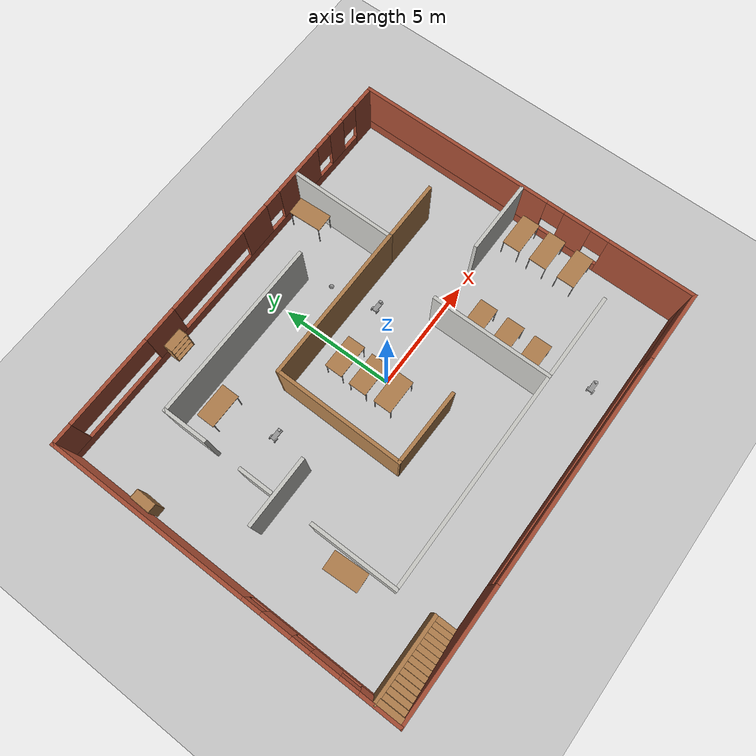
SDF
<sdf version="1.6">
 <world name="default">
  <light name="sun" type="directional">
   <pose>0 0 10 0 -0 0</pose>
   <diffuse>0.8 0.8 0.8 1</diffuse>
   <specular>0.2 0.2 0.2 1</specular>
   <attenuation>
    <range>1000</range>
    <constant>0.9</constant>
    <linear>0.01</linear>
    <quadratic>0.001</quadratic>
   </attenuation>
   <direction>-0.5 0.1 -0.9</direction>
  </light>
  <model name="ground_plane">
   <static>1</static>
   <link name="link">
    <collision name="collision">
     <geometry><plane><normal>0 0 1</normal><size>100 100</size></plane></geometry>
     <surface>
      <contact><collide_bitmask>65535</collide_bitmask></contact>
      <friction><ode><mu>100</mu><mu2>50</mu2></ode></friction>
     </surface>
    </collision>
    <visual name="visual">
     <cast_shadows>0</cast_shadows>
     <geometry><plane><normal>0 0 1</normal><size>100 100</size></plane></geometry>
     <material>
      <script><uri>file://media/materials/scripts/gazebo.material</uri><name>Gazebo/Grey</name></script>
     </material>
    </visual>
   </link>
  </model>
  <gravity>0 0 -9.8</gravity>
  <magnetic_field>6e-06 2.3e-05 -4.2e-05</magnetic_field>
  <atmosphere type="adiabatic"/>
  <physics name="default_physics" default="0" type="ode">
   <max_step_size>0.001</max_step_size>
   <real_time_factor>1</real_time_factor>
   <real_time_update_rate>1000</real_time_update_rate>
  </physics>
  <scene><ambient>0.4 0.4 0.4 1</ambient><background>0.7 0.7 0.7 1</background><shadows>1</shadows></scene>
  <spherical_coordinates>
   <surface_model>EARTH_WGS84</surface_model>
   <latitude_deg>0</latitude_deg>
   <longitude_deg>0</longitude_deg>
   <elevation>0</elevation>
   <heading_deg>0</heading_deg>
  </spherical_coordinates>
  <model name="building">
   <pose>-0.217086 -0.012012 0 0 -0 0</pose>
   <link name="Stairs_1">
    <visual name="Stairs_1_Visual_0">
     <pose>-5.84753 -7.11897 0.083333 0 -0 -1.5708</pose>
     <geometry><box><size>1 0.233333 0.166667</size></box></geometry>
     <material>
      <script><uri>file://media/materials/scripts/gazebo.material</uri><name>Gazebo/Wood</name></script>
      <ambient>1 1 1 1</ambient>
     </material>
     <meta><layer>0</layer></meta>
    </visual>
    <collision name="Stairs_1_Collision_0">
     <geometry><box><size>1 0.233333 0.166667</size></box></geometry>
     <pose>-5.84753 -7.11897 0.083333 0 -0 -1.5708</pose>
    </collision>
    <visual name="Stairs_1_Visual_1">
     <pose>-6.08086 -7.11897 0.25 0 -0 -1.5708</pose>
     <geometry><box><size>1 0.233333 0.166667</size></box></geometry>
     <material>
      <script><uri>file://media/materials/scripts/gazebo.material</uri><name>Gazebo/Wood</name></script>
      <ambient>1 1 1 1</ambient>
     </material>
     <meta><layer>0</layer></meta>
    </visual>
    <collision name="Stairs_1_Collision_1">
     <geometry><box><size>1 0.233333 0.166667</size></box></geometry>
     <pose>-6.08086 -7.11897 0.25 0 -0 -1.5708</pose>
    </collision>
    <visual name="Stairs_1_Visual_2">
     <pose>-6.3142 -7.11897 0.416667 0 -0 -1.5708</pose>
     <geometry><box><size>1 0.233333 0.166667</size></box></geometry>
     <material>
      <script><uri>file://media/materials/scripts/gazebo.material</uri><name>Gazebo/Wood</name></script>
      <ambient>1 1 1 1</ambient>
     </material>
     <meta><layer>0</layer></meta>
    </visual>
    <collision name="Stairs_1_Collision_2">
     <geometry><box><size>1 0.233333 0.166667</size></box></geometry>
     <pose>-6.3142 -7.11897 0.416667 0 -0 -1.5708</pose>
    </collision>
    <visual name="Stairs_1_Visual_3">
     <pose>-6.54753 -7.11897 0.583333 0 -0 -1.5708</pose>
     <geometry><box><size>1 0.233333 0.166667</size></box></geometry>
     <material>
      <script><uri>file://media/materials/scripts/gazebo.material</uri><name>Gazebo/Wood</name></script>
      <ambient>1 1 1 1</ambient>
     </material>
     <meta><layer>0</layer></meta>
    </visual>
    <collision name="Stairs_1_Collision_3">
     <geometry><box><size>1 0.233333 0.166667</size></box></geometry>
     <pose>-6.54753 -7.11897 0.583333 0 -0 -1.5708</pose>
    </collision>
    <visual name="Stairs_1_Visual_4">
     <pose>-6.78086 -7.11897 0.75 0 -0 -1.5708</pose>
     <geometry><box><size>1 0.233333 0.166667</size></box></geometry>
     <material>
      <script><uri>file://media/materials/scripts/gazebo.material</uri><name>Gazebo/Wood</name></script>
      <ambient>1 1 1 1</ambient>
     </material>
     <meta><layer>0</layer></meta>
    </visual>
    <collision name="Stairs_1_Collision_4">
     <geometry><box><size>1 0.233333 0.166667</size></box></geometry>
     <pose>-6.78086 -7.11897 0.75 0 -0 -1.5708</pose>
    </collision>
    <visual name="Stairs_1_Visual_5">
     <pose>-7.0142 -7.11897 0.916667 0 -0 -1.5708</pose>
     <geometry><box><size>1 0.233333 0.166667</size></box></geometry>
     <material>
      <script><uri>file://media/materials/scripts/gazebo.material</uri><name>Gazebo/Wood</name></script>
      <ambient>1 1 1 1</ambient>
     </material>
     <meta><layer>0</layer></meta>
    </visual>
    <collision name="Stairs_1_Collision_5">
     <geometry><box><size>1 0.233333 0.166667</size></box></geometry>
     <pose>-7.0142 -7.11897 0.916667 0 -0 -1.5708</pose>
    </collision>
    <visual name="Stairs_1_Visual_6">
     <pose>-7.24753 -7.11897 1.08333 0 -0 -1.5708</pose>
     <geometry><box><size>1 0.233333 0.166667</size></box></geometry>
     <material>
      <script><uri>file://media/materials/scripts/gazebo.material</uri><name>Gazebo/Wood</name></script>
      <ambient>1 1 1 1</ambient>
     </material>
     <meta><layer>0</layer></meta>
    </visual>
    <collision name="Stairs_1_Collision_6">
     <geometry><box><size>1 0.233333 0.166667</size></box></geometry>
     <pose>-7.24753 -7.11897 1.08333 0 -0 -1.5708</pose>
    </collision>
    <visual name="Stairs_1_Visual_7">
     <pose>-7.48086 -7.11897 1.25 0 -0 -1.5708</pose>
     <geometry><box><size>1 0.233333 0.166667</size></box></geometry>
     <material>
      <script><uri>file://media/materials/scripts/gazebo.material</uri><name>Gazebo/Wood</name></script>
      <ambient>1 1 1 1</ambient>
     </material>
     <meta><layer>0</layer></meta>
    </visual>
    <collision name="Stairs_1_Collision_7">
     <geometry><box><size>1 0.233333 0.166667</size></box></geometry>
     <pose>-7.48086 -7.11897 1.25 0 -0 -1.5708</pose>
    </collision>
    <visual name="Stairs_1_Visual_8">
     <pose>-7.7142 -7.11897 1.41667 0 -0 -1.5708</pose>
     <geometry><box><size>1 0.233333 0.166667</size></box></geometry>
     <material>
      <script><uri>file://media/materials/scripts/gazebo.material</uri><name>Gazebo/Wood</name></script>
      <ambient>1 1 1 1</ambient>
     </material>
     <meta><layer>0</layer></meta>
    </visual>
    <collision name="Stairs_1_Collision_8">
     <geometry><box><size>1 0.233333 0.166667</size></box></geometry>
     <pose>-7.7142 -7.11897 1.41667 0 -0 -1.5708</pose>
    </collision>
    <visual name="Stairs_1_Visual_9">
     <pose>-7.94753 -7.11897 1.58333 0 -0 -1.5708</pose>
     <geometry><box><size>1 0.233333 0.166667</size></box></geometry>
     <material>
      <script><uri>file://media/materials/scripts/gazebo.material</uri><name>Gazebo/Wood</name></script>
      <ambient>1 1 1 1</ambient>
     </material>
     <meta><layer>0</layer></meta>
    </visual>
    <collision name="Stairs_1_Collision_9">
     <geometry><box><size>1 0.233333 0.166667</size></box></geometry>
     <pose>-7.94753 -7.11897 1.58333 0 -0 -1.5708</pose>
    </collision>
    <visual name="Stairs_1_Visual_10">
     <pose>-8.18086 -7.11897 1.75 0 -0 -1.5708</pose>
     <geometry><box><size>1 0.233333 0.166667</size></box></geometry>
     <material>
      <script><uri>file://media/materials/scripts/gazebo.material</uri><name>Gazebo/Wood</name></script>
      <ambient>1 1 1 1</ambient>
     </material>
     <meta><layer>0</layer></meta>
    </visual>
    <collision name="Stairs_1_Collision_10">
     <geometry><box><size>1 0.233333 0.166667</size></box></geometry>
     <pose>-8.18086 -7.11897 1.75 0 -0 -1.5708</pose>
    </collision>
    <visual name="Stairs_1_Visual_11">
     <pose>-8.4142 -7.11897 1.91667 0 -0 -1.5708</pose>
     <geometry><box><size>1 0.233333 0.166667</size></box></geometry>
     <material>
      <script><uri>file://media/materials/scripts/gazebo.material</uri><name>Gazebo/Wood</name></script>
      <ambient>1 1 1 1</ambient>
     </material>
     <meta><layer>0</layer></meta>
    </visual>
    <collision name="Stairs_1_Collision_11">
     <geometry><box><size>1 0.233333 0.166667</size></box></geometry>
     <pose>-8.4142 -7.11897 1.91667 0 -0 -1.5708</pose>
    </collision>
    <visual name="Stairs_1_Visual_12">
     <pose>-8.64753 -7.11897 2.08333 0 -0 -1.5708</pose>
     <geometry><box><size>1 0.233333 0.166667</size></box></geometry>
     <material>
      <script><uri>file://media/materials/scripts/gazebo.material</uri><name>Gazebo/Wood</name></script>
      <ambient>1 1 1 1</ambient>
     </material>
     <meta><layer>0</layer></meta>
    </visual>
    <collision name="Stairs_1_Collision_12">
     <geometry><box><size>1 0.233333 0.166667</size></box></geometry>
     <pose>-8.64753 -7.11897 2.08333 0 -0 -1.5708</pose>
    </collision>
    <visual name="Stairs_1_Visual_13">
     <pose>-8.88086 -7.11897 2.25 0 -0 -1.5708</pose>
     <geometry><box><size>1 0.233333 0.166667</size></box></geometry>
     <material>
      <script><uri>file://media/materials/scripts/gazebo.material</uri><name>Gazebo/Wood</name></script>
      <ambient>1 1 1 1</ambient>
     </material>
     <meta><layer>0</layer></meta>
    </visual>
    <collision name="Stairs_1_Collision_13">
     <geometry><box><size>1 0.233333 0.166667</size></box></geometry>
     <pose>-8.88086 -7.11897 2.25 0 -0 -1.5708</pose>
    </collision>
    <visual name="Stairs_1_Visual_14">
     <pose>-9.1142 -7.11897 2.41667 0 -0 -1.5708</pose>
     <geometry><box><size>1 0.233333 0.166667</size></box></geometry>
     <material>
      <script><uri>file://media/materials/scripts/gazebo.material</uri><name>Gazebo/Wood</name></script>
      <ambient>1 1 1 1</ambient>
     </material>
     <meta><layer>0</layer></meta>
    </visual>
    <collision name="Stairs_1_Collision_14">
     <geometry><box><size>1 0.233333 0.166667</size></box></geometry>
     <pose>-9.1142 -7.11897 2.41667 0 -0 -1.5708</pose>
    </collision>
   </link>
   <link name="Wall_10">
    <pose>-9.3 0 0 0 0 -1.5708</pose>
    <visual name="Wall_10_Visual_0">
     <pose>-3.347 0 1.25 0 -0 0</pose>
     <geometry><box><size>8.80601 0.15 2.5</size></box></geometry>
     <material>
      <script><uri>file://media/materials/scripts/gazebo.material</uri><name>Gazebo/Bricks</name></script>
      <ambient>0.996078 0.47451 0.0196078 1</ambient>
     </material>
     <meta><layer>0</layer></meta>
    </visual>
    <collision name="Wall_10_Collision_0">
     <geometry><box><size>8.80601 0.15 2.5</size></box></geometry>
     <pose>-3.347 0 1.25 0 -0 0</pose>
    </collision>
    <visual name="Wall_10_Visual_1">
     <pose>4.403 0 0.25 0 -0 0</pose>
     <geometry><box><size>6.69399 0.15 0.5</size></box></geometry>
     <material>
      <script><uri>file://media/materials/scripts/gazebo.material</uri><name>Gazebo/Bricks</name></script>
      <ambient>0.996078 0.47451 0.0196078 1</ambient>
     </material>
     <meta><layer>0</layer></meta>
    </visual>
    <collision name="Wall_10_Collision_1">
     <geometry><box><size>6.69399 0.15 0.5</size></box></geometry>
     <pose>4.403 0 0.25 0 -0 0</pose>
    </collision>
    <visual name="Wall_10_Visual_2">
     <pose>2.5021 0 1.5 0 -0 0</pose>
     <geometry><box><size>1.2922 0.15 2</size></box></geometry>
     <material>
      <script><uri>file://media/materials/scripts/gazebo.material</uri><name>Gazebo/Bricks</name></script>
      <ambient>0.996078 0.47451 0.0196078 1</ambient>
     </material>
     <meta><layer>0</layer></meta>
    </visual>
    <collision name="Wall_10_Collision_2">
     <geometry><box><size>1.2922 0.15 2</size></box></geometry>
     <pose>2.5021 0 1.5 0 -0 0</pose>
    </collision>
    <visual name="Wall_10_Visual_3">
     <pose>4.56329 0 1.5 0 -0 0</pose>
     <geometry><box><size>1.23017 0.15 2</size></box></geometry>
     <material>
      <script><uri>file://media/materials/scripts/gazebo.material</uri><name>Gazebo/Bricks</name></script>
      <ambient>0.996078 0.47451 0.0196078 1</ambient>
     </material>
     <meta><layer>0</layer></meta>
    </visual>
    <collision name="Wall_10_Collision_3">
     <geometry><box><size>1.23017 0.15 2</size></box></geometry>
     <pose>4.56329 0 1.5 0 -0 0</pose>
    </collision>
    <visual name="Wall_10_Visual_4">
     <pose>6.86419 0 1.5 0 -0 0</pose>
     <geometry><box><size>1.77163 0.15 2</size></box></geometry>
     <material>
      <script><uri>file://media/materials/scripts/gazebo.material</uri><name>Gazebo/Bricks</name></script>
      <ambient>0.996078 0.47451 0.0196078 1</ambient>
     </material>
     <meta><layer>0</layer></meta>
    </visual>
    <collision name="Wall_10_Collision_4">
     <geometry><box><size>1.77163 0.15 2</size></box></geometry>
     <pose>6.86419 0 1.5 0 -0 0</pose>
    </collision>
    <visual name="Wall_10_Visual_5">
     <pose>1.45601 0 1.9 0 -0 0</pose>
     <geometry><box><size>0.8 0.15 1.2</size></box></geometry>
     <material>
      <script><uri>file://media/materials/scripts/gazebo.material</uri><name>Gazebo/Bricks</name></script>
      <ambient>0.996078 0.47451 0.0196078 1</ambient>
     </material>
     <meta><layer>0</layer></meta>
    </visual>
    <collision name="Wall_10_Collision_5">
     <geometry><box><size>0.8 0.15 1.2</size></box></geometry>
     <pose>1.45601 0 1.9 0 -0 0</pose>
    </collision>
    <visual name="Wall_10_Visual_6">
     <pose>3.5482 0 1.9 0 -0 0</pose>
     <geometry><box><size>0.8 0.15 1.2</size></box></geometry>
     <material>
      <script><uri>file://media/materials/scripts/gazebo.material</uri><name>Gazebo/Bricks</name></script>
      <ambient>0.996078 0.47451 0.0196078 1</ambient>
     </material>
     <meta><layer>0</layer></meta>
    </visual>
    <collision name="Wall_10_Collision_6">
     <geometry><box><size>0.8 0.15 1.2</size></box></geometry>
     <pose>3.5482 0 1.9 0 -0 0</pose>
    </collision>
    <visual name="Wall_10_Visual_7">
     <pose>5.57837 0 1.9 0 -0 0</pose>
     <geometry><box><size>0.8 0.15 1.2</size></box></geometry>
     <material>
      <script><uri>file://media/materials/scripts/gazebo.material</uri><name>Gazebo/Bricks</name></script>
      <ambient>0.996078 0.47451 0.0196078 1</ambient>
     </material>
     <meta><layer>0</layer></meta>
    </visual>
    <collision name="Wall_10_Collision_7">
     <geometry><box><size>0.8 0.15 1.2</size></box></geometry>
     <pose>5.57837 0 1.9 0 -0 0</pose>
    </collision>
   </link>
   <link name="Wall_16">
    <collision name="Wall_16_Collision">
     <geometry><box><size>13.25 0.15 2.5</size></box></geometry>
     <pose>0 0 1.25 0 -0 0</pose>
    </collision>
    <visual name="Wall_16_Visual">
     <pose>0 0 1.25 0 -0 0</pose>
     <geometry><box><size>13.25 0.15 2.5</size></box></geometry>
     <material>
      <script><uri>file://media/materials/scripts/gazebo.material</uri><name>Gazebo/CeilingTiled</name></script>
      <ambient>0.760784 0.662745 0.627451 1</ambient>
     </material>
     <meta><layer>0</layer></meta>
    </visual>
    <pose>0.575 -5.023 0 0 -0 0</pose>
   </link>
   <link name="Wall_20">
    <collision name="Wall_20_Collision">
     <geometry><box><size>7.88472 0.15 2.5</size></box></geometry>
     <pose>0 0 1.25 0 -0 0</pose>
    </collision>
    <visual name="Wall_20_Visual">
     <pose>0 0 1.25 0 -0 0</pose>
     <geometry><box><size>7.88472 0.15 2.5</size></box></geometry>
     <material>
      <script><uri>file://media/materials/scripts/gazebo.material</uri><name>Gazebo/CeilingTiled</name></script>
      <ambient>0.921569 0.807843 0.615686 1</ambient>
     </material>
     <meta><layer>0</layer></meta>
    </visual>
    <pose>-2.1075 5.327 0 0 -0 0</pose>
   </link>
   <link name="Wall_22">
    <collision name="Wall_22_Collision">
     <geometry><box><size>4.75 0.15 2.5</size></box></geometry>
     <pose>0 0 1.25 0 -0 0</pose>
    </collision>
    <visual name="Wall_22_Visual">
     <pose>0 0 1.25 0 -0 0</pose>
     <geometry><box><size>4.75 0.15 2.5</size></box></geometry>
     <material>
      <script><uri>file://media/materials/scripts/gazebo.material</uri><name>Gazebo/CeilingTiled</name></script>
      <ambient>0.921569 0.807843 0.615686 1</ambient>
     </material>
     <meta><layer>0</layer></meta>
    </visual>
    <pose>4.424 5.304 0 0 0 -1.5708</pose>
   </link>
   <link name="Wall_23">
    <collision name="Wall_23_Collision">
     <geometry><box><size>2.75 0.15 2.5</size></box></geometry>
     <pose>0 0 1.25 0 -0 0</pose>
    </collision>
    <visual name="Wall_23_Visual">
     <pose>0 0 1.25 0 -0 0</pose>
     <geometry><box><size>2.75 0.15 2.5</size></box></geometry>
     <material>
      <script><uri>file://media/materials/scripts/gazebo.material</uri><name>Gazebo/Wood</name></script>
      <ambient>1 1 1 1</ambient>
     </material>
     <meta><layer>0</layer></meta>
    </visual>
    <pose>5.724 3.004 0 0 -0 0</pose>
   </link>
   <link name="Wall_25">
    <collision name="Wall_25_Collision">
     <geometry><box><size>6.9618 0.15 2.5</size></box></geometry>
     <pose>0 0 1.25 0 -0 0</pose>
    </collision>
    <visual name="Wall_25_Visual">
     <pose>0 0 1.25 0 -0 0</pose>
     <geometry><box><size>6.9618 0.15 2.5</size></box></geometry>
     <material>
      <script><uri>file://media/materials/scripts/gazebo.material</uri><name>Gazebo/Wood</name></script>
      <ambient>1 1 1 1</ambient>
     </material>
     <meta><layer>0</layer></meta>
    </visual>
    <pose>1.018 3.004 0 0 -0 3.14159</pose>
   </link>
   <link name="Wall_26">
    <collision name="Wall_26_Collision">
     <geometry><box><size>5.6891 0.15 2.5</size></box></geometry>
     <pose>0 0 1.25 0 -0 0</pose>
    </collision>
    <visual name="Wall_26_Visual">
     <pose>0 0 1.25 0 -0 0</pose>
     <geometry><box><size>5.6891 0.15 2.5</size></box></geometry>
     <material>
      <script><uri>file://media/materials/scripts/gazebo.material</uri><name>Gazebo/Wood</name></script>
      <ambient>1 1 1 1</ambient>
     </material>
     <meta><layer>0</layer></meta>
    </visual>
    <pose>-2.419 0.2345 0 0 0 -1.58199</pose>
   </link>
   <link name="Wall_27">
    <collision name="Wall_27_Collision">
     <geometry><box><size>3.31235 0.15 2.5</size></box></geometry>
     <pose>0 0 1.25 0 -0 0</pose>
    </collision>
    <visual name="Wall_27_Visual">
     <pose>0 0 1.25 0 -0 0</pose>
     <geometry><box><size>3.31235 0.15 2.5</size></box></geometry>
     <material>
      <script><uri>file://media/materials/scripts/gazebo.material</uri><name>Gazebo/Wood</name></script>
      <ambient>1 1 1 1</ambient>
     </material>
     <meta><layer>0</layer></meta>
    </visual>
    <pose>-0.869 -2.5655 0 0 0 -0.019289</pose>
   </link>
   <link name="Wall_29">
    <collision name="Wall_29_Collision">
     <geometry><box><size>5.25 0.15 2.5</size></box></geometry>
     <pose>0 0 1.25 0 -0 0</pose>
    </collision>
    <visual name="Wall_29_Visual">
     <pose>0 0 1.25 0 -0 0</pose>
     <geometry><box><size>5.25 0.15 2.5</size></box></geometry>
     <material>
      <script><uri>file://media/materials/scripts/gazebo.material</uri><name>Gazebo/CeilingTiled</name></script>
      <ambient>0.760784 0.662745 0.627451 1</ambient>
     </material>
     <meta><layer>0</layer></meta>
    </visual>
    <pose>3.378 -2.459 0 0 -0 1.5708</pose>
   </link>
   <link name="Wall_31">
    <collision name="Wall_31_Collision">
     <geometry><box><size>3.25 0.15 2.5</size></box></geometry>
     <pose>0 0 1.25 0 -0 0</pose>
    </collision>
    <visual name="Wall_31_Visual">
     <pose>0 0 1.25 0 -0 0</pose>
     <geometry><box><size>3.25 0.15 2.5</size></box></geometry>
     <material>
      <script><uri>file://media/materials/scripts/gazebo.material</uri><name>Gazebo/CeilingTiled</name></script>
      <ambient>0.921569 0.807843 0.615686 1</ambient>
     </material>
     <meta><layer>0</layer></meta>
    </visual>
    <pose>7.643 0.097 0 0 -0 0</pose>
   </link>
   <link name="Wall_33">
    <collision name="Wall_33_Collision">
     <geometry><box><size>2 0.15 2.5</size></box></geometry>
     <pose>0 0 1.25 0 -0 0</pose>
    </collision>
    <visual name="Wall_33_Visual">
     <pose>0 0 1.25 0 -0 0</pose>
     <geometry><box><size>2 0.15 2.5</size></box></geometry>
     <material>
      <script><uri>file://media/materials/scripts/gazebo.material</uri><name>Gazebo/CeilingTiled</name></script>
      <ambient>0.921569 0.807843 0.615686 1</ambient>
     </material>
     <meta><layer>0</layer></meta>
    </visual>
    <pose>-5.975 4.402 0 0 0 -1.5708</pose>
   </link>
   <link name="Wall_35">
    <collision name="Wall_35_Collision">
     <geometry><box><size>3.75 0.15 2.5</size></box></geometry>
     <pose>0 0 1.25 0 -0 0</pose>
    </collision>
    <visual name="Wall_35_Visual">
     <pose>0 0 1.25 0 -0 0</pose>
     <geometry><box><size>3.75 0.15 2.5</size></box></geometry>
     <material>
      <script><uri>file://media/materials/scripts/gazebo.material</uri><name>Gazebo/CeilingTiled</name></script>
      <ambient>0.760784 0.662745 0.627451 1</ambient>
     </material>
     <meta><layer>0</layer></meta>
    </visual>
    <pose>-5.975 -3.223 0 0 0 -1.5708</pose>
   </link>
   <link name="Wall_37">
    <collision name="Wall_37_Collision">
     <geometry><box><size>3 0.15 2.5</size></box></geometry>
     <pose>0 0 1.25 0 -0 0</pose>
    </collision>
    <visual name="Wall_37_Visual">
     <pose>0 0 1.25 0 -0 0</pose>
     <geometry><box><size>3 0.15 2.5</size></box></geometry>
     <material>
      <script><uri>file://media/materials/scripts/gazebo.material</uri><name>Gazebo/CeilingTiled</name></script>
      <ambient>0.760784 0.662745 0.627451 1</ambient>
     </material>
     <meta><layer>0</layer></meta>
    </visual>
    <pose>-5.847 0.267 0 0 -0 0</pose>
   </link>
   <link name="Wall_44">
    <collision name="Wall_44_Collision">
     <geometry><box><size>3.5 0.15 2.5</size></box></geometry>
     <pose>0 0 1.25 0 -0 0</pose>
    </collision>
    <visual name="Wall_44_Visual">
     <pose>0 0 1.25 0 -0 0</pose>
     <geometry><box><size>3.5 0.15 2.5</size></box></geometry>
     <material>
      <script><uri>file://media/materials/scripts/gazebo.material</uri><name>Gazebo/Wood</name></script>
      <ambient>1 1 1 1</ambient>
     </material>
     <meta><layer>0</layer></meta>
    </visual>
    <pose>-7.557 -6.571 0 0 -0 0</pose>
   </link>
   <link name="Wall_46">
    <collision name="Wall_46_Collision">
     <geometry><box><size>1.5 0.15 2.5</size></box></geometry>
     <pose>0 0 1.25 0 -0 0</pose>
    </collision>
    <visual name="Wall_46_Visual">
     <pose>0 0 1.25 0 -0 0</pose>
     <geometry><box><size>1.5 0.15 2.5</size></box></geometry>
     <material>
      <script><uri>file://media/materials/scripts/gazebo.material</uri><name>Gazebo/CeilingTiled</name></script>
      <ambient>0.760784 0.662745 0.627451 1</ambient>
     </material>
     <meta><layer>0</layer></meta>
    </visual>
    <pose>-5.991 1.106 0 0 -0 1.5708</pose>
   </link>
   <link name="Wall_7">
    <pose>0 -7.675 0 0 -0 0</pose>
    <visual name="Wall_7_Visual_0">
     <pose>-6.584 0 1.25 0 -0 0</pose>
     <geometry><box><size>5.582 0.15 2.5</size></box></geometry>
     <material>
      <script><uri>file://media/materials/scripts/gazebo.material</uri><name>Gazebo/Bricks</name></script>
      <ambient>0.996078 0.47451 0.0196078 1</ambient>
     </material>
     <meta><layer>0</layer></meta>
    </visual>
    <collision name="Wall_7_Collision_0">
     <geometry><box><size>5.582 0.15 2.5</size></box></geometry>
     <pose>-6.584 0 1.25 0 -0 0</pose>
    </collision>
    <visual name="Wall_7_Visual_1">
     <pose>2.791 0 0.6 0 -0 0</pose>
     <geometry><box><size>13.168 0.15 1.2</size></box></geometry>
     <material>
      <script><uri>file://media/materials/scripts/gazebo.material</uri><name>Gazebo/Bricks</name></script>
      <ambient>0.996078 0.47451 0.0196078 1</ambient>
     </material>
     <meta><layer>0</layer></meta>
    </visual>
    <collision name="Wall_7_Collision_1">
     <geometry><box><size>13.168 0.15 1.2</size></box></geometry>
     <pose>2.791 0 0.6 0 -0 0</pose>
    </collision>
    <visual name="Wall_7_Visual_2">
     <pose>7.791 0 1.85 0 -0 0</pose>
     <geometry><box><size>3.168 0.15 1.3</size></box></geometry>
     <material>
      <script><uri>file://media/materials/scripts/gazebo.material</uri><name>Gazebo/Bricks</name></script>
      <ambient>0.996078 0.47451 0.0196078 1</ambient>
     </material>
     <meta><layer>0</layer></meta>
    </visual>
    <collision name="Wall_7_Collision_2">
     <geometry><box><size>3.168 0.15 1.3</size></box></geometry>
     <pose>7.791 0 1.85 0 -0 0</pose>
    </collision>
    <visual name="Wall_7_Visual_3">
     <pose>1.207 0 2.15 0 -0 0</pose>
     <geometry><box><size>10 0.15 0.7</size></box></geometry>
     <material>
      <script><uri>file://media/materials/scripts/gazebo.material</uri><name>Gazebo/Bricks</name></script>
      <ambient>0.996078 0.47451 0.0196078 1</ambient>
     </material>
     <meta><layer>0</layer></meta>
    </visual>
    <collision name="Wall_7_Collision_3">
     <geometry><box><size>10 0.15 0.7</size></box></geometry>
     <pose>1.207 0 2.15 0 -0 0</pose>
    </collision>
   </link>
   <link name="Wall_8">
    <pose>9.3 0 0 0 -0 1.5708</pose>
    <visual name="Wall_8_Visual_0">
     <pose>-5.81821 0 1.25 0 -0 0</pose>
     <geometry><box><size>3.86357 0.15 2.5</size></box></geometry>
     <material>
      <script><uri>file://media/materials/scripts/gazebo.material</uri><name>Gazebo/Bricks</name></script>
      <ambient>0.996078 0.47451 0.0196078 1</ambient>
     </material>
     <meta><layer>0</layer></meta>
    </visual>
    <collision name="Wall_8_Collision_0">
     <geometry><box><size>3.86357 0.15 2.5</size></box></geometry>
     <pose>-5.81821 0 1.25 0 -0 0</pose>
    </collision>
    <visual name="Wall_8_Visual_1">
     <pose>1.93179 0 0.25 0 -0 0</pose>
     <geometry><box><size>11.6364 0.15 0.5</size></box></geometry>
     <material>
      <script><uri>file://media/materials/scripts/gazebo.material</uri><name>Gazebo/Bricks</name></script>
      <ambient>0.996078 0.47451 0.0196078 1</ambient>
     </material>
     <meta><layer>0</layer></meta>
    </visual>
    <collision name="Wall_8_Collision_1">
     <geometry><box><size>11.6364 0.15 0.5</size></box></geometry>
     <pose>1.93179 0 0.25 0 -0 0</pose>
    </collision>
    <visual name="Wall_8_Visual_2">
     <pose>-2.47122 0 1.5 0 -0 0</pose>
     <geometry><box><size>1.23042 0.15 2</size></box></geometry>
     <material>
      <script><uri>file://media/materials/scripts/gazebo.material</uri><name>Gazebo/Bricks</name></script>
      <ambient>0.996078 0.47451 0.0196078 1</ambient>
     </material>
     <meta><layer>0</layer></meta>
    </visual>
    <collision name="Wall_8_Collision_2">
     <geometry><box><size>1.23042 0.15 2</size></box></geometry>
     <pose>-2.47122 0 1.5 0 -0 0</pose>
    </collision>
    <visual name="Wall_8_Visual_3">
     <pose>3.347 0 1.5 0 -0 0</pose>
     <geometry><box><size>8.80601 0.15 2</size></box></geometry>
     <material>
      <script><uri>file://media/materials/scripts/gazebo.material</uri><name>Gazebo/Bricks</name></script>
      <ambient>0.996078 0.47451 0.0196078 1</ambient>
     </material>
     <meta><layer>0</layer></meta>
    </visual>
    <collision name="Wall_8_Collision_3">
     <geometry><box><size>8.80601 0.15 2</size></box></geometry>
     <pose>3.347 0 1.5 0 -0 0</pose>
    </collision>
    <visual name="Wall_8_Visual_4">
     <pose>-3.48643 0 1.9 0 -0 0</pose>
     <geometry><box><size>0.8 0.15 1.2</size></box></geometry>
     <material>
      <script><uri>file://media/materials/scripts/gazebo.material</uri><name>Gazebo/Bricks</name></script>
      <ambient>0.996078 0.47451 0.0196078 1</ambient>
     </material>
     <meta><layer>0</layer></meta>
    </visual>
    <collision name="Wall_8_Collision_4">
     <geometry><box><size>0.8 0.15 1.2</size></box></geometry>
     <pose>-3.48643 0 1.9 0 -0 0</pose>
    </collision>
    <visual name="Wall_8_Visual_5">
     <pose>-1.45601 0 1.9 0 -0 0</pose>
     <geometry><box><size>0.8 0.15 1.2</size></box></geometry>
     <material>
      <script><uri>file://media/materials/scripts/gazebo.material</uri><name>Gazebo/Bricks</name></script>
      <ambient>0.996078 0.47451 0.0196078 1</ambient>
     </material>
     <meta><layer>0</layer></meta>
    </visual>
    <collision name="Wall_8_Collision_5">
     <geometry><box><size>0.8 0.15 1.2</size></box></geometry>
     <pose>-1.45601 0 1.9 0 -0 0</pose>
    </collision>
   </link>
   <link name="Wall_9">
    <pose>0 7.675 0 0 -0 3.14159</pose>
    <visual name="Wall_9_Visual_0">
     <pose>-8.79645 0 1.25 0 -0 0</pose>
     <geometry><box><size>1.15709 0.15 2.5</size></box></geometry>
     <material>
      <script><uri>file://media/materials/scripts/gazebo.material</uri><name>Gazebo/Bricks</name></script>
      <ambient>0.996078 0.47451 0.0196078 1</ambient>
     </material>
     <meta><layer>0</layer></meta>
    </visual>
    <collision name="Wall_9_Collision_0">
     <geometry><box><size>1.15709 0.15 2.5</size></box></geometry>
     <pose>-8.79645 0 1.25 0 -0 0</pose>
    </collision>
    <visual name="Wall_9_Visual_1">
     <pose>0.578547 0 0.25 0 -0 0</pose>
     <geometry><box><size>17.5929 0.15 0.5</size></box></geometry>
     <material>
      <script><uri>file://media/materials/scripts/gazebo.material</uri><name>Gazebo/Bricks</name></script>
      <ambient>0.996078 0.47451 0.0196078 1</ambient>
     </material>
     <meta><layer>0</layer></meta>
    </visual>
    <collision name="Wall_9_Collision_1">
     <geometry><box><size>17.5929 0.15 0.5</size></box></geometry>
     <pose>0.578547 0 0.25 0 -0 0</pose>
    </collision>
    <visual name="Wall_9_Visual_2">
     <pose>-6.98728 0 1.5 0 -0 0</pose>
     <geometry><box><size>0.861253 0.15 2</size></box></geometry>
     <material>
      <script><uri>file://media/materials/scripts/gazebo.material</uri><name>Gazebo/Bricks</name></script>
      <ambient>0.996078 0.47451 0.0196078 1</ambient>
     </material>
     <meta><layer>0</layer></meta>
    </visual>
    <collision name="Wall_9_Collision_2">
     <geometry><box><size>0.861253 0.15 2</size></box></geometry>
     <pose>-6.98728 0 1.5 0 -0 0</pose>
    </collision>
    <visual name="Wall_9_Visual_3">
     <pose>-4.55693 0 1.5 0 -0 0</pose>
     <geometry><box><size>2.39945 0.15 2</size></box></geometry>
     <material>
      <script><uri>file://media/materials/scripts/gazebo.material</uri><name>Gazebo/Bricks</name></script>
      <ambient>0.996078 0.47451 0.0196078 1</ambient>
     </material>
     <meta><layer>0</layer></meta>
    </visual>
    <collision name="Wall_9_Collision_3">
     <geometry><box><size>2.39945 0.15 2</size></box></geometry>
     <pose>-4.55693 0 1.5 0 -0 0</pose>
    </collision>
    <visual name="Wall_9_Visual_4">
     <pose>-1.84984 0 1.5 0 -0 0</pose>
     <geometry><box><size>1.41473 0.15 2</size></box></geometry>
     <material>
      <script><uri>file://media/materials/scripts/gazebo.material</uri><name>Gazebo/Bricks</name></script>
      <ambient>0.996078 0.47451 0.0196078 1</ambient>
     </material>
     <meta><layer>0</layer></meta>
    </visual>
    <collision name="Wall_9_Collision_4">
     <geometry><box><size>1.41473 0.15 2</size></box></geometry>
     <pose>-1.84984 0 1.5 0 -0 0</pose>
    </collision>
    <visual name="Wall_9_Visual_5">
     <pose>3.62628 0 1.5 0 -0 0</pose>
     <geometry><box><size>1.53751 0.15 2</size></box></geometry>
     <material>
      <script><uri>file://media/materials/scripts/gazebo.material</uri><name>Gazebo/Bricks</name></script>
      <ambient>0.996078 0.47451 0.0196078 1</ambient>
     </material>
     <meta><layer>0</layer></meta>
    </visual>
    <collision name="Wall_9_Collision_5">
     <geometry><box><size>1.53751 0.15 2</size></box></geometry>
     <pose>3.62628 0 1.5 0 -0 0</pose>
    </collision>
    <visual name="Wall_9_Visual_6">
     <pose>8.88502 0 1.5 0 -0 0</pose>
     <geometry><box><size>0.979966 0.15 2</size></box></geometry>
     <material>
      <script><uri>file://media/materials/scripts/gazebo.material</uri><name>Gazebo/Bricks</name></script>
      <ambient>0.996078 0.47451 0.0196078 1</ambient>
     </material>
     <meta><layer>0</layer></meta>
    </visual>
    <collision name="Wall_9_Collision_6">
     <geometry><box><size>0.979966 0.15 2</size></box></geometry>
     <pose>8.88502 0 1.5 0 -0 0</pose>
    </collision>
    <visual name="Wall_9_Visual_7">
     <pose>-7.81791 0 1.9 0 -0 0</pose>
     <geometry><box><size>0.8 0.15 1.2</size></box></geometry>
     <material>
      <script><uri>file://media/materials/scripts/gazebo.material</uri><name>Gazebo/Bricks</name></script>
      <ambient>0.996078 0.47451 0.0196078 1</ambient>
     </material>
     <meta><layer>0</layer></meta>
    </visual>
    <collision name="Wall_9_Collision_7">
     <geometry><box><size>0.8 0.15 1.2</size></box></geometry>
     <pose>-7.81791 0 1.9 0 -0 0</pose>
    </collision>
    <visual name="Wall_9_Visual_8">
     <pose>-6.15665 0 1.9 0 -0 0</pose>
     <geometry><box><size>0.8 0.15 1.2</size></box></geometry>
     <material>
      <script><uri>file://media/materials/scripts/gazebo.material</uri><name>Gazebo/Bricks</name></script>
      <ambient>0.996078 0.47451 0.0196078 1</ambient>
     </material>
     <meta><layer>0</layer></meta>
    </visual>
    <collision name="Wall_9_Collision_8">
     <geometry><box><size>0.8 0.15 1.2</size></box></geometry>
     <pose>-6.15665 0 1.9 0 -0 0</pose>
    </collision>
    <visual name="Wall_9_Visual_9">
     <pose>-2.9572 0 1.9 0 -0 0</pose>
     <geometry><box><size>0.8 0.15 1.2</size></box></geometry>
     <material>
      <script><uri>file://media/materials/scripts/gazebo.material</uri><name>Gazebo/Bricks</name></script>
      <ambient>0.996078 0.47451 0.0196078 1</ambient>
     </material>
     <meta><layer>0</layer></meta>
    </visual>
    <collision name="Wall_9_Collision_9">
     <geometry><box><size>0.8 0.15 1.2</size></box></geometry>
     <pose>-2.9572 0 1.9 0 -0 0</pose>
    </collision>
    <visual name="Wall_9_Visual_10">
     <pose>0.857525 0 1.9 0 -0 0</pose>
     <geometry><box><size>4 0.15 1.2</size></box></geometry>
     <material>
      <script><uri>file://media/materials/scripts/gazebo.material</uri><name>Gazebo/Bricks</name></script>
      <ambient>0.996078 0.47451 0.0196078 1</ambient>
     </material>
     <meta><layer>0</layer></meta>
    </visual>
    <collision name="Wall_9_Collision_10">
     <geometry><box><size>4 0.15 1.2</size></box></geometry>
     <pose>0.857525 0 1.9 0 -0 0</pose>
    </collision>
    <visual name="Wall_9_Visual_11">
     <pose>6.39503 0 1.9 0 -0 0</pose>
     <geometry><box><size>4 0.15 1.2</size></box></geometry>
     <material>
      <script><uri>file://media/materials/scripts/gazebo.material</uri><name>Gazebo/Bricks</name></script>
      <ambient>0.996078 0.47451 0.0196078 1</ambient>
     </material>
     <meta><layer>0</layer></meta>
    </visual>
    <collision name="Wall_9_Collision_11">
     <geometry><box><size>4 0.15 1.2</size></box></geometry>
     <pose>6.39503 0 1.9 0 -0 0</pose>
    </collision>
   </link>
   <static>1</static>
  </model>
  <model name="table">
   <static>1</static>
   <link name="link">
    <collision name="surface">
     <pose>0 0 1 0 -0 0</pose>
     <geometry><box><size>1.5 0.8 0.03</size></box></geometry>
     <surface><friction><ode><mu>0.6</mu><mu2>0.6</mu2></ode></friction></surface>
    </collision>
    <visual name="visual1">
     <pose>0 0 1 0 -0 0</pose>
     <geometry><box><size>1.5 0.8 0.03</size></box></geometry>
     <material>
      <script><uri>file://media/materials/scripts/gazebo.material</uri><name>Gazebo/Wood</name></script>
     </material>
    </visual>
    <collision name="front_left_leg">
     <pose>0.68 0.38 0.5 0 -0 0</pose>
     <geometry><cylinder><radius>0.02</radius><length>1</length></cylinder></geometry>
    </collision>
    <visual name="front_left_leg">
     <pose>0.68 0.38 0.5 0 -0 0</pose>
     <geometry><cylinder><radius>0.02</radius><length>1</length></cylinder></geometry>
     <material>
      <script><uri>file://media/materials/scripts/gazebo.material</uri><name>Gazebo/Grey</name></script>
     </material>
    </visual>
    <collision name="front_right_leg">
     <pose>0.68 -0.38 0.5 0 -0 0</pose>
     <geometry><cylinder><radius>0.02</radius><length>1</length></cylinder></geometry>
    </collision>
    <visual name="front_right_leg">
     <pose>0.68 -0.38 0.5 0 -0 0</pose>
     <geometry><cylinder><radius>0.02</radius><length>1</length></cylinder></geometry>
     <material>
      <script><uri>file://media/materials/scripts/gazebo.material</uri><name>Gazebo/Grey</name></script>
     </material>
    </visual>
    <collision name="back_right_leg">
     <pose>-0.68 -0.38 0.5 0 -0 0</pose>
     <geometry><cylinder><radius>0.02</radius><length>1</length></cylinder></geometry>
    </collision>
    <visual name="back_right_leg">
     <pose>-0.68 -0.38 0.5 0 -0 0</pose>
     <geometry><cylinder><radius>0.02</radius><length>1</length></cylinder></geometry>
     <material>
      <script><uri>file://media/materials/scripts/gazebo.material</uri><name>Gazebo/Grey</name></script>
     </material>
    </visual>
    <collision name="back_left_leg">
     <pose>-0.68 0.38 0.5 0 -0 0</pose>
     <geometry><cylinder><radius>0.02</radius><length>1</length></cylinder></geometry>
    </collision>
    <visual name="back_left_leg">
     <pose>-0.68 0.38 0.5 0 -0 0</pose>
     <geometry><cylinder><radius>0.02</radius><length>1</length></cylinder></geometry>
     <material>
      <script><uri>file://media/materials/scripts/gazebo.material</uri><name>Gazebo/Grey</name></script>
     </material>
    </visual>
   </link>
   <pose>4.02135 -1.52151 0 0 -0 0</pose>
  </model>
  <model name="table_clone">
   <static>1</static>
   <link name="link">
    <collision name="surface">
     <pose>0 0 1 0 -0 0</pose>
     <geometry><box><size>1.5 0.8 0.03</size></box></geometry>
     <surface><friction><ode><mu>0.6</mu><mu2>0.6</mu2></ode></friction></surface>
    </collision>
    <visual name="visual1">
     <pose>0 0 1 0 -0 0</pose>
     <geometry><box><size>1.5 0.8 0.03</size></box></geometry>
     <material>
      <script><uri>file://media/materials/scripts/gazebo.material</uri><name>Gazebo/Wood</name></script>
     </material>
    </visual>
    <collision name="front_left_leg">
     <pose>0.68 0.38 0.5 0 -0 0</pose>
     <geometry><cylinder><radius>0.02</radius><length>1</length></cylinder></geometry>
    </collision>
    <visual name="front_left_leg">
     <pose>0.68 0.38 0.5 0 -0 0</pose>
     <geometry><cylinder><radius>0.02</radius><length>1</length></cylinder></geometry>
     <material>
      <script><uri>file://media/materials/scripts/gazebo.material</uri><name>Gazebo/Grey</name></script>
     </material>
    </visual>
    <collision name="front_right_leg">
     <pose>0.68 -0.38 0.5 0 -0 0</pose>
     <geometry><cylinder><radius>0.02</radius><length>1</length></cylinder></geometry>
    </collision>
    <visual name="front_right_leg">
     <pose>0.68 -0.38 0.5 0 -0 0</pose>
     <geometry><cylinder><radius>0.02</radius><length>1</length></cylinder></geometry>
     <material>
      <script><uri>file://media/materials/scripts/gazebo.material</uri><name>Gazebo/Grey</name></script>
     </material>
    </visual>
    <collision name="back_right_leg">
     <pose>-0.68 -0.38 0.5 0 -0 0</pose>
     <geometry><cylinder><radius>0.02</radius><length>1</length></cylinder></geometry>
    </collision>
    <visual name="back_right_leg">
     <pose>-0.68 -0.38 0.5 0 -0 0</pose>
     <geometry><cylinder><radius>0.02</radius><length>1</length></cylinder></geometry>
     <material>
      <script><uri>file://media/materials/scripts/gazebo.material</uri><name>Gazebo/Grey</name></script>
     </material>
    </visual>
    <collision name="back_left_leg">
     <pose>-0.68 0.38 0.5 0 -0 0</pose>
     <geometry><cylinder><radius>0.02</radius><length>1</length></cylinder></geometry>
    </collision>
    <visual name="back_left_leg">
     <pose>-0.68 0.38 0.5 0 -0 0</pose>
     <geometry><cylinder><radius>0.02</radius><length>1</length></cylinder></geometry>
     <material>
      <script><uri>file://media/materials/scripts/gazebo.material</uri><name>Gazebo/Grey</name></script>
     </material>
    </visual>
   </link>
   <pose>4.02135 -2.7982 0 0 -0 0</pose>
  </model>
  <model name="table_clone_0">
   <static>1</static>
   <link name="link">
    <collision name="surface">
     <pose>0 0 1 0 -0 0</pose>
     <geometry><box><size>1.5 0.8 0.03</size></box></geometry>
     <surface><friction><ode><mu>0.6</mu><mu2>0.6</mu2></ode></friction></surface>
    </collision>
    <visual name="visual1">
     <pose>0 0 1 0 -0 0</pose>
     <geometry><box><size>1.5 0.8 0.03</size></box></geometry>
     <material>
      <script><uri>file://media/materials/scripts/gazebo.material</uri><name>Gazebo/Wood</name></script>
     </material>
    </visual>
    <collision name="front_left_leg">
     <pose>0.68 0.38 0.5 0 -0 0</pose>
     <geometry><cylinder><radius>0.02</radius><length>1</length></cylinder></geometry>
    </collision>
    <visual name="front_left_leg">
     <pose>0.68 0.38 0.5 0 -0 0</pose>
     <geometry><cylinder><radius>0.02</radius><length>1</length></cylinder></geometry>
     <material>
      <script><uri>file://media/materials/scripts/gazebo.material</uri><name>Gazebo/Grey</name></script>
     </material>
    </visual>
    <collision name="front_right_leg">
     <pose>0.68 -0.38 0.5 0 -0 0</pose>
     <geometry><cylinder><radius>0.02</radius><length>1</length></cylinder></geometry>
    </collision>
    <visual name="front_right_leg">
     <pose>0.68 -0.38 0.5 0 -0 0</pose>
     <geometry><cylinder><radius>0.02</radius><length>1</length></cylinder></geometry>
     <material>
      <script><uri>file://media/materials/scripts/gazebo.material</uri><name>Gazebo/Grey</name></script>
     </material>
    </visual>
    <collision name="back_right_leg">
     <pose>-0.68 -0.38 0.5 0 -0 0</pose>
     <geometry><cylinder><radius>0.02</radius><length>1</length></cylinder></geometry>
    </collision>
    <visual name="back_right_leg">
     <pose>-0.68 -0.38 0.5 0 -0 0</pose>
     <geometry><cylinder><radius>0.02</radius><length>1</length></cylinder></geometry>
     <material>
      <script><uri>file://media/materials/scripts/gazebo.material</uri><name>Gazebo/Grey</name></script>
     </material>
    </visual>
    <collision name="back_left_leg">
     <pose>-0.68 0.38 0.5 0 -0 0</pose>
     <geometry><cylinder><radius>0.02</radius><length>1</length></cylinder></geometry>
    </collision>
    <visual name="back_left_leg">
     <pose>-0.68 0.38 0.5 0 -0 0</pose>
     <geometry><cylinder><radius>0.02</radius><length>1</length></cylinder></geometry>
     <material>
      <script><uri>file://media/materials/scripts/gazebo.material</uri><name>Gazebo/Grey</name></script>
     </material>
    </visual>
   </link>
   <pose>4.02135 -4.0721 0 0 -0 0</pose>
  </model>
  <model name="table_clone_1">
   <static>1</static>
   <link name="link">
    <collision name="surface">
     <pose>0 0 1 0 -0 0</pose>
     <geometry><box><size>1.5 0.8 0.03</size></box></geometry>
     <surface><friction><ode><mu>0.6</mu><mu2>0.6</mu2></ode></friction></surface>
    </collision>
    <visual name="visual1">
     <pose>0 0 1 0 -0 0</pose>
     <geometry><box><size>1.5 0.8 0.03</size></box></geometry>
     <material>
      <script><uri>file://media/materials/scripts/gazebo.material</uri><name>Gazebo/Wood</name></script>
     </material>
    </visual>
    <collision name="front_left_leg">
     <pose>0.68 0.38 0.5 0 -0 0</pose>
     <geometry><cylinder><radius>0.02</radius><length>1</length></cylinder></geometry>
    </collision>
    <visual name="front_left_leg">
     <pose>0.68 0.38 0.5 0 -0 0</pose>
     <geometry><cylinder><radius>0.02</radius><length>1</length></cylinder></geometry>
     <material>
      <script><uri>file://media/materials/scripts/gazebo.material</uri><name>Gazebo/Grey</name></script>
     </material>
    </visual>
    <collision name="front_right_leg">
     <pose>0.68 -0.38 0.5 0 -0 0</pose>
     <geometry><cylinder><radius>0.02</radius><length>1</length></cylinder></geometry>
    </collision>
    <visual name="front_right_leg">
     <pose>0.68 -0.38 0.5 0 -0 0</pose>
     <geometry><cylinder><radius>0.02</radius><length>1</length></cylinder></geometry>
     <material>
      <script><uri>file://media/materials/scripts/gazebo.material</uri><name>Gazebo/Grey</name></script>
     </material>
    </visual>
    <collision name="back_right_leg">
     <pose>-0.68 -0.38 0.5 0 -0 0</pose>
     <geometry><cylinder><radius>0.02</radius><length>1</length></cylinder></geometry>
    </collision>
    <visual name="back_right_leg">
     <pose>-0.68 -0.38 0.5 0 -0 0</pose>
     <geometry><cylinder><radius>0.02</radius><length>1</length></cylinder></geometry>
     <material>
      <script><uri>file://media/materials/scripts/gazebo.material</uri><name>Gazebo/Grey</name></script>
     </material>
    </visual>
    <collision name="back_left_leg">
     <pose>-0.68 0.38 0.5 0 -0 0</pose>
     <geometry><cylinder><radius>0.02</radius><length>1</length></cylinder></geometry>
    </collision>
    <visual name="back_left_leg">
     <pose>-0.68 0.38 0.5 0 -0 0</pose>
     <geometry><cylinder><radius>0.02</radius><length>1</length></cylinder></geometry>
     <material>
      <script><uri>file://media/materials/scripts/gazebo.material</uri><name>Gazebo/Grey</name></script>
     </material>
    </visual>
   </link>
   <pose>8.1253 -0.794744 0 0 -0 0</pose>
  </model>
  <model name="table_clone_2">
   <static>1</static>
   <link name="link">
    <collision name="surface">
     <pose>0 0 1 0 -0 0</pose>
     <geometry><box><size>1.5 0.8 0.03</size></box></geometry>
     <surface><friction><ode><mu>0.6</mu><mu2>0.6</mu2></ode></friction></surface>
    </collision>
    <visual name="visual1">
     <pose>0 0 1 0 -0 0</pose>
     <geometry><box><size>1.5 0.8 0.03</size></box></geometry>
     <material>
      <script><uri>file://media/materials/scripts/gazebo.material</uri><name>Gazebo/Wood</name></script>
     </material>
    </visual>
    <collision name="front_left_leg">
     <pose>0.68 0.38 0.5 0 -0 0</pose>
     <geometry><cylinder><radius>0.02</radius><length>1</length></cylinder></geometry>
    </collision>
    <visual name="front_left_leg">
     <pose>0.68 0.38 0.5 0 -0 0</pose>
     <geometry><cylinder><radius>0.02</radius><length>1</length></cylinder></geometry>
     <material>
      <script><uri>file://media/materials/scripts/gazebo.material</uri><name>Gazebo/Grey</name></script>
     </material>
    </visual>
    <collision name="front_right_leg">
     <pose>0.68 -0.38 0.5 0 -0 0</pose>
     <geometry><cylinder><radius>0.02</radius><length>1</length></cylinder></geometry>
    </collision>
    <visual name="front_right_leg">
     <pose>0.68 -0.38 0.5 0 -0 0</pose>
     <geometry><cylinder><radius>0.02</radius><length>1</length></cylinder></geometry>
     <material>
      <script><uri>file://media/materials/scripts/gazebo.material</uri><name>Gazebo/Grey</name></script>
     </material>
    </visual>
    <collision name="back_right_leg">
     <pose>-0.68 -0.38 0.5 0 -0 0</pose>
     <geometry><cylinder><radius>0.02</radius><length>1</length></cylinder></geometry>
    </collision>
    <visual name="back_right_leg">
     <pose>-0.68 -0.38 0.5 0 -0 0</pose>
     <geometry><cylinder><radius>0.02</radius><length>1</length></cylinder></geometry>
     <material>
      <script><uri>file://media/materials/scripts/gazebo.material</uri><name>Gazebo/Grey</name></script>
     </material>
    </visual>
    <collision name="back_left_leg">
     <pose>-0.68 0.38 0.5 0 -0 0</pose>
     <geometry><cylinder><radius>0.02</radius><length>1</length></cylinder></geometry>
    </collision>
    <visual name="back_left_leg">
     <pose>-0.68 0.38 0.5 0 -0 0</pose>
     <geometry><cylinder><radius>0.02</radius><length>1</length></cylinder></geometry>
     <material>
      <script><uri>file://media/materials/scripts/gazebo.material</uri><name>Gazebo/Grey</name></script>
     </material>
    </visual>
   </link>
   <pose>8.1253 -2.05917 0 0 -0 0</pose>
  </model>
  <model name="table_clone_3">
   <static>1</static>
   <link name="link">
    <collision name="surface">
     <pose>0 0 1 0 -0 0</pose>
     <geometry><box><size>1.5 0.8 0.03</size></box></geometry>
     <surface><friction><ode><mu>0.6</mu><mu2>0.6</mu2></ode></friction></surface>
    </collision>
    <visual name="visual1">
     <pose>0 0 1 0 -0 0</pose>
     <geometry><box><size>1.5 0.8 0.03</size></box></geometry>
     <material>
      <script><uri>file://media/materials/scripts/gazebo.material</uri><name>Gazebo/Wood</name></script>
     </material>
    </visual>
    <collision name="front_left_leg">
     <pose>0.68 0.38 0.5 0 -0 0</pose>
     <geometry><cylinder><radius>0.02</radius><length>1</length></cylinder></geometry>
    </collision>
    <visual name="front_left_leg">
     <pose>0.68 0.38 0.5 0 -0 0</pose>
     <geometry><cylinder><radius>0.02</radius><length>1</length></cylinder></geometry>
     <material>
      <script><uri>file://media/materials/scripts/gazebo.material</uri><name>Gazebo/Grey</name></script>
     </material>
    </visual>
    <collision name="front_right_leg">
     <pose>0.68 -0.38 0.5 0 -0 0</pose>
     <geometry><cylinder><radius>0.02</radius><length>1</length></cylinder></geometry>
    </collision>
    <visual name="front_right_leg">
     <pose>0.68 -0.38 0.5 0 -0 0</pose>
     <geometry><cylinder><radius>0.02</radius><length>1</length></cylinder></geometry>
     <material>
      <script><uri>file://media/materials/scripts/gazebo.material</uri><name>Gazebo/Grey</name></script>
     </material>
    </visual>
    <collision name="back_right_leg">
     <pose>-0.68 -0.38 0.5 0 -0 0</pose>
     <geometry><cylinder><radius>0.02</radius><length>1</length></cylinder></geometry>
    </collision>
    <visual name="back_right_leg">
     <pose>-0.68 -0.38 0.5 0 -0 0</pose>
     <geometry><cylinder><radius>0.02</radius><length>1</length></cylinder></geometry>
     <material>
      <script><uri>file://media/materials/scripts/gazebo.material</uri><name>Gazebo/Grey</name></script>
     </material>
    </visual>
    <collision name="back_left_leg">
     <pose>-0.68 0.38 0.5 0 -0 0</pose>
     <geometry><cylinder><radius>0.02</radius><length>1</length></cylinder></geometry>
    </collision>
    <visual name="back_left_leg">
     <pose>-0.68 0.38 0.5 0 -0 0</pose>
     <geometry><cylinder><radius>0.02</radius><length>1</length></cylinder></geometry>
     <material>
      <script><uri>file://media/materials/scripts/gazebo.material</uri><name>Gazebo/Grey</name></script>
     </material>
    </visual>
   </link>
   <pose>8.1253 -3.39167 0 0 -0 0</pose>
  </model>
  <model name="table_clone_4">
   <static>1</static>
   <link name="link">
    <collision name="surface">
     <pose>0 0 1 0 -0 0</pose>
     <geometry><box><size>1.5 0.8 0.03</size></box></geometry>
     <surface><friction><ode><mu>0.6</mu><mu2>0.6</mu2></ode></friction></surface>
    </collision>
    <visual name="visual1">
     <pose>0 0 1 0 -0 0</pose>
     <geometry><box><size>1.5 0.8 0.03</size></box></geometry>
     <material>
      <script><uri>file://media/materials/scripts/gazebo.material</uri><name>Gazebo/Wood</name></script>
     </material>
    </visual>
    <collision name="front_left_leg">
     <pose>0.68 0.38 0.5 0 -0 0</pose>
     <geometry><cylinder><radius>0.02</radius><length>1</length></cylinder></geometry>
    </collision>
    <visual name="front_left_leg">
     <pose>0.68 0.38 0.5 0 -0 0</pose>
     <geometry><cylinder><radius>0.02</radius><length>1</length></cylinder></geometry>
     <material>
      <script><uri>file://media/materials/scripts/gazebo.material</uri><name>Gazebo/Grey</name></script>
     </material>
    </visual>
    <collision name="front_right_leg">
     <pose>0.68 -0.38 0.5 0 -0 0</pose>
     <geometry><cylinder><radius>0.02</radius><length>1</length></cylinder></geometry>
    </collision>
    <visual name="front_right_leg">
     <pose>0.68 -0.38 0.5 0 -0 0</pose>
     <geometry><cylinder><radius>0.02</radius><length>1</length></cylinder></geometry>
     <material>
      <script><uri>file://media/materials/scripts/gazebo.material</uri><name>Gazebo/Grey</name></script>
     </material>
    </visual>
    <collision name="back_right_leg">
     <pose>-0.68 -0.38 0.5 0 -0 0</pose>
     <geometry><cylinder><radius>0.02</radius><length>1</length></cylinder></geometry>
    </collision>
    <visual name="back_right_leg">
     <pose>-0.68 -0.38 0.5 0 -0 0</pose>
     <geometry><cylinder><radius>0.02</radius><length>1</length></cylinder></geometry>
     <material>
      <script><uri>file://media/materials/scripts/gazebo.material</uri><name>Gazebo/Grey</name></script>
     </material>
    </visual>
    <collision name="back_left_leg">
     <pose>-0.68 0.38 0.5 0 -0 0</pose>
     <geometry><cylinder><radius>0.02</radius><length>1</length></cylinder></geometry>
    </collision>
    <visual name="back_left_leg">
     <pose>-0.68 0.38 0.5 0 -0 0</pose>
     <geometry><cylinder><radius>0.02</radius><length>1</length></cylinder></geometry>
     <material>
      <script><uri>file://media/materials/scripts/gazebo.material</uri><name>Gazebo/Grey</name></script>
     </material>
    </visual>
   </link>
   <pose>-0.355759 1.73772 0 0 -0 0</pose>
  </model>
  <model name="table_clone_5">
   <static>1</static>
   <link name="link">
    <collision name="surface">
     <pose>0 0 1 0 -0 0</pose>
     <geometry><box><size>1.5 0.8 0.03</size></box></geometry>
     <surface><friction><ode><mu>0.6</mu><mu2>0.6</mu2></ode></friction></surface>
    </collision>
    <visual name="visual1">
     <pose>0 0 1 0 -0 0</pose>
     <geometry><box><size>1.5 0.8 0.03</size></box></geometry>
     <material>
      <script><uri>file://media/materials/scripts/gazebo.material</uri><name>Gazebo/Wood</name></script>
     </material>
    </visual>
    <collision name="front_left_leg">
     <pose>0.68 0.38 0.5 0 -0 0</pose>
     <geometry><cylinder><radius>0.02</radius><length>1</length></cylinder></geometry>
    </collision>
    <visual name="front_left_leg">
     <pose>0.68 0.38 0.5 0 -0 0</pose>
     <geometry><cylinder><radius>0.02</radius><length>1</length></cylinder></geometry>
     <material>
      <script><uri>file://media/materials/scripts/gazebo.material</uri><name>Gazebo/Grey</name></script>
     </material>
    </visual>
    <collision name="front_right_leg">
     <pose>0.68 -0.38 0.5 0 -0 0</pose>
     <geometry><cylinder><radius>0.02</radius><length>1</length></cylinder></geometry>
    </collision>
    <visual name="front_right_leg">
     <pose>0.68 -0.38 0.5 0 -0 0</pose>
     <geometry><cylinder><radius>0.02</radius><length>1</length></cylinder></geometry>
     <material>
      <script><uri>file://media/materials/scripts/gazebo.material</uri><name>Gazebo/Grey</name></script>
     </material>
    </visual>
    <collision name="back_right_leg">
     <pose>-0.68 -0.38 0.5 0 -0 0</pose>
     <geometry><cylinder><radius>0.02</radius><length>1</length></cylinder></geometry>
    </collision>
    <visual name="back_right_leg">
     <pose>-0.68 -0.38 0.5 0 -0 0</pose>
     <geometry><cylinder><radius>0.02</radius><length>1</length></cylinder></geometry>
     <material>
      <script><uri>file://media/materials/scripts/gazebo.material</uri><name>Gazebo/Grey</name></script>
     </material>
    </visual>
    <collision name="back_left_leg">
     <pose>-0.68 0.38 0.5 0 -0 0</pose>
     <geometry><cylinder><radius>0.02</radius><length>1</length></cylinder></geometry>
    </collision>
    <visual name="back_left_leg">
     <pose>-0.68 0.38 0.5 0 -0 0</pose>
     <geometry><cylinder><radius>0.02</radius><length>1</length></cylinder></geometry>
     <material>
      <script><uri>file://media/materials/scripts/gazebo.material</uri><name>Gazebo/Grey</name></script>
     </material>
    </visual>
   </link>
   <pose>-0.391017 0.561094 0 0 -0 0</pose>
  </model>
  <model name="table_clone_6">
   <static>1</static>
   <link name="link">
    <collision name="surface">
     <pose>0 0 1 0 -0 0</pose>
     <geometry><box><size>1.5 0.8 0.03</size></box></geometry>
     <surface><friction><ode><mu>0.6</mu><mu2>0.6</mu2></ode></friction></surface>
    </collision>
    <visual name="visual1">
     <pose>0 0 1 0 -0 0</pose>
     <geometry><box><size>1.5 0.8 0.03</size></box></geometry>
     <material>
      <script><uri>file://media/materials/scripts/gazebo.material</uri><name>Gazebo/Wood</name></script>
     </material>
    </visual>
    <collision name="front_left_leg">
     <pose>0.68 0.38 0.5 0 -0 0</pose>
     <geometry><cylinder><radius>0.02</radius><length>1</length></cylinder></geometry>
    </collision>
    <visual name="front_left_leg">
     <pose>0.68 0.38 0.5 0 -0 0</pose>
     <geometry><cylinder><radius>0.02</radius><length>1</length></cylinder></geometry>
     <material>
      <script><uri>file://media/materials/scripts/gazebo.material</uri><name>Gazebo/Grey</name></script>
     </material>
    </visual>
    <collision name="front_right_leg">
     <pose>0.68 -0.38 0.5 0 -0 0</pose>
     <geometry><cylinder><radius>0.02</radius><length>1</length></cylinder></geometry>
    </collision>
    <visual name="front_right_leg">
     <pose>0.68 -0.38 0.5 0 -0 0</pose>
     <geometry><cylinder><radius>0.02</radius><length>1</length></cylinder></geometry>
     <material>
      <script><uri>file://media/materials/scripts/gazebo.material</uri><name>Gazebo/Grey</name></script>
     </material>
    </visual>
    <collision name="back_right_leg">
     <pose>-0.68 -0.38 0.5 0 -0 0</pose>
     <geometry><cylinder><radius>0.02</radius><length>1</length></cylinder></geometry>
    </collision>
    <visual name="back_right_leg">
     <pose>-0.68 -0.38 0.5 0 -0 0</pose>
     <geometry><cylinder><radius>0.02</radius><length>1</length></cylinder></geometry>
     <material>
      <script><uri>file://media/materials/scripts/gazebo.material</uri><name>Gazebo/Grey</name></script>
     </material>
    </visual>
    <collision name="back_left_leg">
     <pose>-0.68 0.38 0.5 0 -0 0</pose>
     <geometry><cylinder><radius>0.02</radius><length>1</length></cylinder></geometry>
    </collision>
    <visual name="back_left_leg">
     <pose>-0.68 0.38 0.5 0 -0 0</pose>
     <geometry><cylinder><radius>0.02</radius><length>1</length></cylinder></geometry>
     <material>
      <script><uri>file://media/materials/scripts/gazebo.material</uri><name>Gazebo/Grey</name></script>
     </material>
    </visual>
   </link>
   <pose>-0.375932 -0.615177 0 0 -0 0</pose>
  </model>
  <model name="table_clone_4_clone">
   <static>1</static>
   <link name="link">
    <collision name="surface">
     <pose>0 0 1 0 -0 0</pose>
     <geometry><box><size>1.5 0.8 0.03</size></box></geometry>
     <surface><friction><ode><mu>0.6</mu><mu2>0.6</mu2></ode></friction></surface>
    </collision>
    <visual name="visual1">
     <pose>0 0 1 0 -0 0</pose>
     <geometry><box><size>1.5 0.8 0.03</size></box></geometry>
     <material>
      <script><uri>file://media/materials/scripts/gazebo.material</uri><name>Gazebo/Wood</name></script>
     </material>
    </visual>
    <collision name="front_left_leg">
     <pose>0.68 0.38 0.5 0 -0 0</pose>
     <geometry><cylinder><radius>0.02</radius><length>1</length></cylinder></geometry>
    </collision>
    <visual name="front_left_leg">
     <pose>0.68 0.38 0.5 0 -0 0</pose>
     <geometry><cylinder><radius>0.02</radius><length>1</length></cylinder></geometry>
     <material>
      <script><uri>file://media/materials/scripts/gazebo.material</uri><name>Gazebo/Grey</name></script>
     </material>
    </visual>
    <collision name="front_right_leg">
     <pose>0.68 -0.38 0.5 0 -0 0</pose>
     <geometry><cylinder><radius>0.02</radius><length>1</length></cylinder></geometry>
    </collision>
    <visual name="front_right_leg">
     <pose>0.68 -0.38 0.5 0 -0 0</pose>
     <geometry><cylinder><radius>0.02</radius><length>1</length></cylinder></geometry>
     <material>
      <script><uri>file://media/materials/scripts/gazebo.material</uri><name>Gazebo/Grey</name></script>
     </material>
    </visual>
    <collision name="back_right_leg">
     <pose>-0.68 -0.38 0.5 0 -0 0</pose>
     <geometry><cylinder><radius>0.02</radius><length>1</length></cylinder></geometry>
    </collision>
    <visual name="back_right_leg">
     <pose>-0.68 -0.38 0.5 0 -0 0</pose>
     <geometry><cylinder><radius>0.02</radius><length>1</length></cylinder></geometry>
     <material>
      <script><uri>file://media/materials/scripts/gazebo.material</uri><name>Gazebo/Grey</name></script>
     </material>
    </visual>
    <collision name="back_left_leg">
     <pose>-0.68 0.38 0.5 0 -0 0</pose>
     <geometry><cylinder><radius>0.02</radius><length>1</length></cylinder></geometry>
    </collision>
    <visual name="back_left_leg">
     <pose>-0.68 0.38 0.5 0 -0 0</pose>
     <geometry><cylinder><radius>0.02</radius><length>1</length></cylinder></geometry>
     <material>
      <script><uri>file://media/materials/scripts/gazebo.material</uri><name>Gazebo/Grey</name></script>
     </material>
    </visual>
   </link>
   <pose>-4.81486 4.39365 0 0 -0 0</pose>
  </model>
  <model name="table_clone_4_clone_0">
   <static>1</static>
   <link name="link">
    <collision name="surface">
     <pose>0 0 1 0 -0 0</pose>
     <geometry><box><size>1.5 0.8 0.03</size></box></geometry>
     <surface><friction><ode><mu>0.6</mu><mu2>0.6</mu2></ode></friction></surface>
    </collision>
    <visual name="visual1">
     <pose>0 0 1 0 -0 0</pose>
     <geometry><box><size>1.5 0.8 0.03</size></box></geometry>
     <material>
      <script><uri>file://media/materials/scripts/gazebo.material</uri><name>Gazebo/Wood</name></script>
     </material>
    </visual>
    <collision name="front_left_leg">
     <pose>0.68 0.38 0.5 0 -0 0</pose>
     <geometry><cylinder><radius>0.02</radius><length>1</length></cylinder></geometry>
    </collision>
    <visual name="front_left_leg">
     <pose>0.68 0.38 0.5 0 -0 0</pose>
     <geometry><cylinder><radius>0.02</radius><length>1</length></cylinder></geometry>
     <material>
      <script><uri>file://media/materials/scripts/gazebo.material</uri><name>Gazebo/Grey</name></script>
     </material>
    </visual>
    <collision name="front_right_leg">
     <pose>0.68 -0.38 0.5 0 -0 0</pose>
     <geometry><cylinder><radius>0.02</radius><length>1</length></cylinder></geometry>
    </collision>
    <visual name="front_right_leg">
     <pose>0.68 -0.38 0.5 0 -0 0</pose>
     <geometry><cylinder><radius>0.02</radius><length>1</length></cylinder></geometry>
     <material>
      <script><uri>file://media/materials/scripts/gazebo.material</uri><name>Gazebo/Grey</name></script>
     </material>
    </visual>
    <collision name="back_right_leg">
     <pose>-0.68 -0.38 0.5 0 -0 0</pose>
     <geometry><cylinder><radius>0.02</radius><length>1</length></cylinder></geometry>
    </collision>
    <visual name="back_right_leg">
     <pose>-0.68 -0.38 0.5 0 -0 0</pose>
     <geometry><cylinder><radius>0.02</radius><length>1</length></cylinder></geometry>
     <material>
      <script><uri>file://media/materials/scripts/gazebo.material</uri><name>Gazebo/Grey</name></script>
     </material>
    </visual>
    <collision name="back_left_leg">
     <pose>-0.68 0.38 0.5 0 -0 0</pose>
     <geometry><cylinder><radius>0.02</radius><length>1</length></cylinder></geometry>
    </collision>
    <visual name="back_left_leg">
     <pose>-0.68 0.38 0.5 0 -0 0</pose>
     <geometry><cylinder><radius>0.02</radius><length>1</length></cylinder></geometry>
     <material>
      <script><uri>file://media/materials/scripts/gazebo.material</uri><name>Gazebo/Grey</name></script>
     </material>
    </visual>
   </link>
   <pose>3.65435 6.65379 0 0 -0 1.61882</pose>
  </model>
  <model name="bookshelf">
   <static>1</static>
   <link name="link">
    <inertial><mass>1</mass></inertial>
    <collision name="back">
     <pose>0 0.005 0.6 0 -0 0</pose>
     <geometry><box><size>0.9 0.01 1.2</size></box></geometry>
    </collision>
    <visual name="visual1">
     <pose>0 0.005 0.6 0 -0 0</pose>
     <geometry><box><size>0.9 0.01 1.2</size></box></geometry>
     <material>
      <script><uri>file://media/materials/scripts/gazebo.material</uri><name>Gazebo/Wood</name></script>
     </material>
    </visual>
    <collision name="left_side">
     <pose>0.45 -0.195 0.6 0 -0 0</pose>
     <geometry><box><size>0.02 0.4 1.2</size></box></geometry>
    </collision>
    <visual name="visual2">
     <pose>0.45 -0.195 0.6 0 -0 0</pose>
     <geometry><box><size>0.02 0.4 1.2</size></box></geometry>
     <material>
      <script><uri>file://media/materials/scripts/gazebo.material</uri><name>Gazebo/Wood</name></script>
     </material>
    </visual>
    <collision name="right_side">
     <pose>-0.45 -0.195 0.6 0 -0 0</pose>
     <geometry><box><size>0.02 0.4 1.2</size></box></geometry>
    </collision>
    <visual name="visual3">
     <pose>-0.45 -0.195 0.6 0 -0 0</pose>
     <geometry><box><size>0.02 0.4 1.2</size></box></geometry>
     <material>
      <script><uri>file://media/materials/scripts/gazebo.material</uri><name>Gazebo/Wood</name></script>
     </material>
    </visual>
    <collision name="bottom">
     <pose>0 -0.195 0.03 0 -0 0</pose>
     <geometry><box><size>0.88 0.4 0.06</size></box></geometry>
    </collision>
    <visual name="visual4">
     <pose>0 -0.195 0.03 0 -0 0</pose>
     <geometry><box><size>0.88 0.4 0.06</size></box></geometry>
     <material>
      <script><uri>file://media/materials/scripts/gazebo.material</uri><name>Gazebo/Wood</name></script>
     </material>
    </visual>
    <collision name="top">
     <pose>0 -0.195 1.19 0 -0 0</pose>
     <geometry><box><size>0.88 0.4 0.02</size></box></geometry>
    </collision>
    <visual name="visual5">
     <pose>0 -0.195 1.19 0 -0 0</pose>
     <geometry><box><size>0.88 0.4 0.02</size></box></geometry>
     <material>
      <script><uri>file://media/materials/scripts/gazebo.material</uri><name>Gazebo/Wood</name></script>
     </material>
    </visual>
    <collision name="low_shelf">
     <pose>0 -0.195 0.43 0 -0 0</pose>
     <geometry><box><size>0.88 0.4 0.02</size></box></geometry>
    </collision>
    <visual name="visual6">
     <pose>0 -0.195 0.43 0 -0 0</pose>
     <geometry><box><size>0.88 0.4 0.02</size></box></geometry>
     <material>
      <script><uri>file://media/materials/scripts/gazebo.material</uri><name>Gazebo/Wood</name></script>
     </material>
    </visual>
    <collision name="high_shelf">
     <pose>0 -0.195 0.8 0 -0 0</pose>
     <geometry><box><size>0.88 0.4 0.02</size></box></geometry>
    </collision>
    <visual name="visual7">
     <pose>0 -0.195 0.8 0 -0 0</pose>
     <geometry><box><size>0.88 0.4 0.02</size></box></geometry>
     <material>
      <script><uri>file://media/materials/scripts/gazebo.material</uri><name>Gazebo/Wood</name></script>
     </material>
    </visual>
   </link>
   <pose>-9.38503 4.19513 0 0 -0 1.54267</pose>
  </model>
  <model name="bookshelf_0">
   <static>1</static>
   <link name="link">
    <inertial><mass>1</mass></inertial>
    <collision name="back">
     <pose>0 0.005 0.6 0 -0 0</pose>
     <geometry><box><size>0.9 0.01 1.2</size></box></geometry>
    </collision>
    <visual name="visual1">
     <pose>0 0.005 0.6 0 -0 0</pose>
     <geometry><box><size>0.9 0.01 1.2</size></box></geometry>
     <material>
      <script><uri>file://media/materials/scripts/gazebo.material</uri><name>Gazebo/Wood</name></script>
     </material>
    </visual>
    <collision name="left_side">
     <pose>0.45 -0.195 0.6 0 -0 0</pose>
     <geometry><box><size>0.02 0.4 1.2</size></box></geometry>
    </collision>
    <visual name="visual2">
     <pose>0.45 -0.195 0.6 0 -0 0</pose>
     <geometry><box><size>0.02 0.4 1.2</size></box></geometry>
     <material>
      <script><uri>file://media/materials/scripts/gazebo.material</uri><name>Gazebo/Wood</name></script>
     </material>
    </visual>
    <collision name="right_side">
     <pose>-0.45 -0.195 0.6 0 -0 0</pose>
     <geometry><box><size>0.02 0.4 1.2</size></box></geometry>
    </collision>
    <visual name="visual3">
     <pose>-0.45 -0.195 0.6 0 -0 0</pose>
     <geometry><box><size>0.02 0.4 1.2</size></box></geometry>
     <material>
      <script><uri>file://media/materials/scripts/gazebo.material</uri><name>Gazebo/Wood</name></script>
     </material>
    </visual>
    <collision name="bottom">
     <pose>0 -0.195 0.03 0 -0 0</pose>
     <geometry><box><size>0.88 0.4 0.06</size></box></geometry>
    </collision>
    <visual name="visual4">
     <pose>0 -0.195 0.03 0 -0 0</pose>
     <geometry><box><size>0.88 0.4 0.06</size></box></geometry>
     <material>
      <script><uri>file://media/materials/scripts/gazebo.material</uri><name>Gazebo/Wood</name></script>
     </material>
    </visual>
    <collision name="top">
     <pose>0 -0.195 1.19 0 -0 0</pose>
     <geometry><box><size>0.88 0.4 0.02</size></box></geometry>
    </collision>
    <visual name="visual5">
     <pose>0 -0.195 1.19 0 -0 0</pose>
     <geometry><box><size>0.88 0.4 0.02</size></box></geometry>
     <material>
      <script><uri>file://media/materials/scripts/gazebo.material</uri><name>Gazebo/Wood</name></script>
     </material>
    </visual>
    <collision name="low_shelf">
     <pose>0 -0.195 0.43 0 -0 0</pose>
     <geometry><box><size>0.88 0.4 0.02</size></box></geometry>
    </collision>
    <visual name="visual6">
     <pose>0 -0.195 0.43 0 -0 0</pose>
     <geometry><box><size>0.88 0.4 0.02</size></box></geometry>
     <material>
      <script><uri>file://media/materials/scripts/gazebo.material</uri><name>Gazebo/Wood</name></script>
     </material>
    </visual>
    <collision name="high_shelf">
     <pose>0 -0.195 0.8 0 -0 0</pose>
     <geometry><box><size>0.88 0.4 0.02</size></box></geometry>
    </collision>
    <visual name="visual7">
     <pose>0 -0.195 0.8 0 -0 0</pose>
     <geometry><box><size>0.88 0.4 0.02</size></box></geometry>
     <material>
      <script><uri>file://media/materials/scripts/gazebo.material</uri><name>Gazebo/Wood</name></script>
     </material>
    </visual>
   </link>
   <pose>-3.81555 7.54531 0 0 -0 0</pose>
  </model>
  <model name="table_clone_4_clone_0_clone">
   <static>1</static>
   <link name="link">
    <collision name="surface">
     <pose>0 0 1 0 -0 0</pose>
     <geometry><box><size>1.5 0.8 0.03</size></box></geometry>
     <surface><friction><ode><mu>0.6</mu><mu2>0.6</mu2></ode></friction></surface>
    </collision>
    <visual name="visual1">
     <pose>0 0 1 0 -0 0</pose>
     <geometry><box><size>1.5 0.8 0.03</size></box></geometry>
     <material>
      <script><uri>file://media/materials/scripts/gazebo.material</uri><name>Gazebo/Wood</name></script>
     </material>
    </visual>
    <collision name="front_left_leg">
     <pose>0.68 0.38 0.5 0 -0 0</pose>
     <geometry><cylinder><radius>0.02</radius><length>1</length></cylinder></geometry>
    </collision>
    <visual name="front_left_leg">
     <pose>0.68 0.38 0.5 0 -0 0</pose>
     <geometry><cylinder><radius>0.02</radius><length>1</length></cylinder></geometry>
     <material>
      <script><uri>file://media/materials/scripts/gazebo.material</uri><name>Gazebo/Grey</name></script>
     </material>
    </visual>
    <collision name="front_right_leg">
     <pose>0.68 -0.38 0.5 0 -0 0</pose>
     <geometry><cylinder><radius>0.02</radius><length>1</length></cylinder></geometry>
    </collision>
    <visual name="front_right_leg">
     <pose>0.68 -0.38 0.5 0 -0 0</pose>
     <geometry><cylinder><radius>0.02</radius><length>1</length></cylinder></geometry>
     <material>
      <script><uri>file://media/materials/scripts/gazebo.material</uri><name>Gazebo/Grey</name></script>
     </material>
    </visual>
    <collision name="back_right_leg">
     <pose>-0.68 -0.38 0.5 0 -0 0</pose>
     <geometry><cylinder><radius>0.02</radius><length>1</length></cylinder></geometry>
    </collision>
    <visual name="back_right_leg">
     <pose>-0.68 -0.38 0.5 0 -0 0</pose>
     <geometry><cylinder><radius>0.02</radius><length>1</length></cylinder></geometry>
     <material>
      <script><uri>file://media/materials/scripts/gazebo.material</uri><name>Gazebo/Grey</name></script>
     </material>
    </visual>
    <collision name="back_left_leg">
     <pose>-0.68 0.38 0.5 0 -0 0</pose>
     <geometry><cylinder><radius>0.02</radius><length>1</length></cylinder></geometry>
    </collision>
    <visual name="back_left_leg">
     <pose>-0.68 0.38 0.5 0 -0 0</pose>
     <geometry><cylinder><radius>0.02</radius><length>1</length></cylinder></geometry>
     <material>
      <script><uri>file://media/materials/scripts/gazebo.material</uri><name>Gazebo/Grey</name></script>
     </material>
    </visual>
   </link>
   <pose>-6.73397 -3.22442 0 0 -0 1.61882</pose>
  </model>
  <model name="white_ball">
   <link name="link_0">
    <inertial>
     <mass>1</mass>
     <inertia><ixx>0.1</ixx><ixy>0</ixy><ixz>0</ixz><iyy>0.1</iyy><iyz>0</iyz><izz>0.1</izz></inertia>
    </inertial>
    <visual name="visual">
     <geometry><sphere><radius>0.1</radius></sphere></geometry>
     <material>
      <lighting>1</lighting>
      <script><uri>file://media/materials/scripts/gazebo.material</uri><name>Gazebo/Grey</name></script>
      <shader type="pixel"><normal_map>__default__</normal_map></shader>
      <ambient>1 1 1 1</ambient>
      <diffuse>1 1 1 1</diffuse>
      <specular>1 1 1 1</specular>
      <emissive>1 1 1 1</emissive>
     </material>
    </visual>
    <collision name="collision">
     <geometry><sphere><radius>0.1</radius></sphere></geometry>
     <surface>
      <friction>
       <ode><mu>1</mu><mu2>1</mu2><fdir1>0 0 0</fdir1><slip1>0</slip1><slip2>0</slip2></ode>
       <torsional>
        <coefficient>1</coefficient>
        <patch_radius>0</patch_radius>
        <surface_radius>0</surface_radius>
        <use_patch_radius>1</use_patch_radius>
        <ode><slip>0</slip></ode>
       </torsional>
      </friction>
      <bounce><restitution_coefficient>0</restitution_coefficient><threshold>1e+06</threshold></bounce>
      <contact>
       <collide_without_contact>0</collide_without_contact>
       <collide_without_contact_bitmask>1</collide_without_contact_bitmask>
       <collide_bitmask>1</collide_bitmask>
       <ode>
        <soft_cfm>0</soft_cfm>
        <soft_erp>0.2</soft_erp>
        <kp>1e+13</kp>
        <kd>1</kd>
        <max_vel>0.01</max_vel>
        <min_depth>0</min_depth>
       </ode>
       <bullet>
        <split_impulse>1</split_impulse>
        <split_impulse_penetration_threshold>-0.01</split_impulse_penetration_threshold>
        <soft_cfm>0</soft_cfm>
        <soft_erp>0.2</soft_erp>
        <kp>1e+13</kp>
        <kd>1</kd>
       </bullet>
      </contact>
     </surface>
    </collision>
   </link>
   <static>0</static>
   <pose>1.92531 4.25571 0.1 0 -0 0</pose>
  </model>
  <model name="TriRobot">
   <link name="link_2">
    <pose>0.001674 0.000657 -0.001317 0 -0 0</pose>
    <inertial>
     <mass>1</mass>
     <inertia>
      <ixx>0.166667</ixx>
      <ixy>0</ixy>
      <ixz>0</ixz>
      <iyy>0.166667</iyy>
      <iyz>0</iyz>
      <izz>0.166667</izz>
     </inertia>
    </inertial>
    <visual name="visual">
     <geometry><box><size>0.5 0.2 0.1</size></box></geometry>
     <material>
      <lighting>1</lighting>
      <script><uri>file://media/materials/scripts/gazebo.material</uri><name>Gazebo/Grey</name></script>
      <shader type="pixel"><normal_map>__default__</normal_map></shader>
      <ambient>0.3 0.3 0.3 1</ambient>
      <diffuse>0.7 0.7 0.7 1</diffuse>
      <specular>0.01 0.01 0.01 1</specular>
      <emissive>0 0 0 1</emissive>
     </material>
    </visual>
    <collision name="collision">
     <geometry><box><size>0.5 0.2 0.1</size></box></geometry>
     <surface>
      <friction>
       <ode><mu>1</mu><mu2>1</mu2><fdir1>0 0 0</fdir1><slip1>0</slip1><slip2>0</slip2></ode>
       <torsional>
        <coefficient>1</coefficient>
        <patch_radius>0</patch_radius>
        <surface_radius>0</surface_radius>
        <use_patch_radius>1</use_patch_radius>
        <ode><slip>0</slip></ode>
       </torsional>
      </friction>
      <bounce><restitution_coefficient>0</restitution_coefficient><threshold>1e+06</threshold></bounce>
      <contact>
       <collide_without_contact>0</collide_without_contact>
       <collide_without_contact_bitmask>1</collide_without_contact_bitmask>
       <collide_bitmask>1</collide_bitmask>
       <ode>
        <soft_cfm>0</soft_cfm>
        <soft_erp>0.2</soft_erp>
        <kp>1e+13</kp>
        <kd>1</kd>
        <max_vel>0.01</max_vel>
        <min_depth>0</min_depth>
       </ode>
       <bullet>
        <split_impulse>1</split_impulse>
        <split_impulse_penetration_threshold>-0.01</split_impulse_penetration_threshold>
        <soft_cfm>0</soft_cfm>
        <soft_erp>0.2</soft_erp>
        <kp>1e+13</kp>
        <kd>1</kd>
       </bullet>
      </contact>
     </surface>
    </collision>
   </link>
   <link name="link_3">
    <pose>-0.198326 0.125657 -0.001317 1.5707 -0 0</pose>
    <inertial>
     <mass>1</mass>
     <inertia><ixx>0.145833</ixx><ixy>0</ixy><ixz>0</ixz><iyy>0.145833</iyy><iyz>0</iyz><izz>0.125</izz></inertia>
    </inertial>
    <visual name="visual">
     <geometry><cylinder><radius>0.1</radius><length>0.05</length></cylinder></geometry>
     <material>
      <lighting>1</lighting>
      <script><uri>file://media/materials/scripts/gazebo.material</uri><name>Gazebo/Grey</name></script>
      <shader type="pixel"><normal_map>__default__</normal_map></shader>
      <ambient>0.3 0.3 0.3 1</ambient>
      <diffuse>0.7 0.7 0.7 1</diffuse>
      <specular>0.01 0.01 0.01 1</specular>
      <emissive>0 0 0 1</emissive>
     </material>
    </visual>
    <collision name="collision">
     <geometry><cylinder><radius>0.1</radius><length>0.05</length></cylinder></geometry>
     <surface>
      <friction>
       <ode><mu>1</mu><mu2>1</mu2><fdir1>0 0 0</fdir1><slip1>0</slip1><slip2>0</slip2></ode>
       <torsional>
        <coefficient>1</coefficient>
        <patch_radius>0</patch_radius>
        <surface_radius>0</surface_radius>
        <use_patch_radius>1</use_patch_radius>
        <ode><slip>0</slip></ode>
       </torsional>
      </friction>
      <bounce><restitution_coefficient>0</restitution_coefficient><threshold>1e+06</threshold></bounce>
      <contact>
       <collide_without_contact>0</collide_without_contact>
       <collide_without_contact_bitmask>1</collide_without_contact_bitmask>
       <collide_bitmask>1</collide_bitmask>
       <ode>
        <soft_cfm>0</soft_cfm>
        <soft_erp>0.2</soft_erp>
        <kp>1e+13</kp>
        <kd>1</kd>
        <max_vel>0.01</max_vel>
        <min_depth>0</min_depth>
       </ode>
       <bullet>
        <split_impulse>1</split_impulse>
        <split_impulse_penetration_threshold>-0.01</split_impulse_penetration_threshold>
        <soft_cfm>0</soft_cfm>
        <soft_erp>0.2</soft_erp>
        <kp>1e+13</kp>
        <kd>1</kd>
       </bullet>
      </contact>
     </surface>
    </collision>
   </link>
   <link name="link_3_clone">
    <pose>-0.198326 -0.124343 -0.001317 1.5707 -0 0</pose>
    <inertial>
     <mass>1</mass>
     <inertia><ixx>0.145833</ixx><ixy>0</ixy><ixz>0</ixz><iyy>0.145833</iyy><iyz>0</iyz><izz>0.125</izz></inertia>
    </inertial>
    <visual name="visual">
     <geometry><cylinder><radius>0.1</radius><length>0.05</length></cylinder></geometry>
     <material>
      <lighting>1</lighting>
      <script><uri>file://media/materials/scripts/gazebo.material</uri><name>Gazebo/Grey</name></script>
      <shader type="pixel"><normal_map>__default__</normal_map></shader>
      <ambient>0.3 0.3 0.3 1</ambient>
      <diffuse>0.7 0.7 0.7 1</diffuse>
      <specular>0.01 0.01 0.01 1</specular>
      <emissive>0 0 0 1</emissive>
     </material>
    </visual>
    <collision name="collision">
     <geometry><cylinder><radius>0.1</radius><length>0.05</length></cylinder></geometry>
     <surface>
      <friction>
       <ode><mu>1</mu><mu2>1</mu2><fdir1>0 0 0</fdir1><slip1>0</slip1><slip2>0</slip2></ode>
       <torsional>
        <coefficient>1</coefficient>
        <patch_radius>0</patch_radius>
        <surface_radius>0</surface_radius>
        <use_patch_radius>1</use_patch_radius>
        <ode><slip>0</slip></ode>
       </torsional>
      </friction>
      <bounce><restitution_coefficient>0</restitution_coefficient><threshold>1e+06</threshold></bounce>
      <contact>
       <collide_without_contact>0</collide_without_contact>
       <collide_without_contact_bitmask>1</collide_without_contact_bitmask>
       <collide_bitmask>1</collide_bitmask>
       <ode>
        <soft_cfm>0</soft_cfm>
        <soft_erp>0.2</soft_erp>
        <kp>1e+13</kp>
        <kd>1</kd>
        <max_vel>0.01</max_vel>
        <min_depth>0</min_depth>
       </ode>
       <bullet>
        <split_impulse>1</split_impulse>
        <split_impulse_penetration_threshold>-0.01</split_impulse_penetration_threshold>
        <soft_cfm>0</soft_cfm>
        <soft_erp>0.2</soft_erp>
        <kp>1e+13</kp>
        <kd>1</kd>
       </bullet>
      </contact>
     </surface>
    </collision>
   </link>
   <link name="link_5">
    <pose>0.201674 0.000657 -0.051317 0 -0 0</pose>
    <inertial>
     <mass>1</mass>
     <inertia><ixx>0.1</ixx><ixy>0</ixy><ixz>0</ixz><iyy>0.1</iyy><iyz>0</iyz><izz>0.1</izz></inertia>
    </inertial>
    <visual name="visual">
     <geometry><sphere><radius>0.05</radius></sphere></geometry>
     <material>
      <lighting>1</lighting>
      <script><uri>file://media/materials/scripts/gazebo.material</uri><name>Gazebo/Grey</name></script>
      <shader type="pixel"><normal_map>__default__</normal_map></shader>
      <ambient>0.3 0.3 0.3 1</ambient>
      <diffuse>0.7 0.7 0.7 1</diffuse>
      <specular>0.01 0.01 0.01 1</specular>
      <emissive>0 0 0 1</emissive>
     </material>
    </visual>
    <collision name="collision">
     <geometry><sphere><radius>0.05</radius></sphere></geometry>
     <surface>
      <friction>
       <ode><mu>1</mu><mu2>1</mu2><fdir1>0 0 0</fdir1><slip1>0</slip1><slip2>0</slip2></ode>
       <torsional>
        <coefficient>1</coefficient>
        <patch_radius>0</patch_radius>
        <surface_radius>0</surface_radius>
        <use_patch_radius>1</use_patch_radius>
        <ode><slip>0</slip></ode>
       </torsional>
      </friction>
      <bounce><restitution_coefficient>0</restitution_coefficient><threshold>1e+06</threshold></bounce>
      <contact>
       <collide_without_contact>0</collide_without_contact>
       <collide_without_contact_bitmask>1</collide_without_contact_bitmask>
       <collide_bitmask>1</collide_bitmask>
       <ode>
        <soft_cfm>0</soft_cfm>
        <soft_erp>0.2</soft_erp>
        <kp>1e+13</kp>
        <kd>1</kd>
        <max_vel>0.01</max_vel>
        <min_depth>0</min_depth>
       </ode>
       <bullet>
        <split_impulse>1</split_impulse>
        <split_impulse_penetration_threshold>-0.01</split_impulse_penetration_threshold>
        <soft_cfm>0</soft_cfm>
        <soft_erp>0.2</soft_erp>
        <kp>1e+13</kp>
        <kd>1</kd>
       </bullet>
      </contact>
     </surface>
    </collision>
   </link>
   <model name="depth_camera">
    <link name="link">
     <pose>0 0 0.05 0 -0 0</pose>
     <inertial>
      <mass>0.1</mass>
      <inertia>
       <ixx>0.000166667</ixx>
       <iyy>0.000166667</iyy>
       <izz>0.000166667</izz>
       <ixy>0</ixy>
       <ixz>0</ixz>
       <iyz>0</iyz>
      </inertia>
     </inertial>
     <collision name="collision"><geometry><box><size>0.1 0.1 0.1</size></box></geometry></collision>
     <visual name="visual"><geometry><box><size>0.1 0.1 0.1</size></box></geometry></visual>
     <sensor name="camera" type="depth">
      <camera name="__default__">
       <horizontal_fov>1.047</horizontal_fov>
       <image><width>320</width><height>240</height></image>
       <clip><near>0.1</near><far>100</far></clip>
      </camera>
      <always_on>1</always_on>
      <update_rate>30</update_rate>
      <visualize>1</visualize>
     </sensor>
    </link>
    <pose>0.193306 -0.00263 0.055267 0 -0 0</pose>
   </model>
   <joint name="link_2_JOINT_10" type="revolute">
    <parent>link_2</parent>
    <child>link_3</child>
    <axis>
     <xyz>0 0 1</xyz>
     <use_parent_model_frame>0</use_parent_model_frame>
     <limit>
      <lower>-1.79769e+308</lower>
      <upper>1.79769e+308</upper>
      <effort>-1</effort>
      <velocity>-1</velocity>
     </limit>
     <dynamics>
      <spring_reference>0</spring_reference>
      <spring_stiffness>0</spring_stiffness>
      <damping>0</damping>
      <friction>0</friction>
     </dynamics>
    </axis>
    <physics>
     <ode><limit><cfm>0</cfm><erp>0.2</erp></limit><suspension><cfm>0</cfm><erp>0.2</erp></suspension></ode>
    </physics>
   </joint>
   <joint name="link_2_JOINT_11" type="revolute">
    <parent>link_2</parent>
    <child>link_3_clone</child>
    <pose>0 0 0 0 -0.01 0</pose>
    <axis>
     <xyz>0 0 -1</xyz>
     <use_parent_model_frame>0</use_parent_model_frame>
     <limit>
      <lower>-1.79769e+308</lower>
      <upper>1.79769e+308</upper>
      <effort>-1</effort>
      <velocity>-1</velocity>
     </limit>
     <dynamics>
      <spring_reference>0</spring_reference>
      <spring_stiffness>0</spring_stiffness>
      <damping>0</damping>
      <friction>0</friction>
     </dynamics>
    </axis>
    <physics>
     <ode><limit><cfm>0</cfm><erp>0.2</erp></limit><suspension><cfm>0</cfm><erp>0.2</erp></suspension></ode>
    </physics>
   </joint>
   <joint name="link_2_JOINT_12" type="ball">
    <parent>link_2</parent>
    <child>link_5</child>
    <physics>
     <ode><limit><cfm>0</cfm><erp>0.2</erp></limit><suspension><cfm>0</cfm><erp>0.2</erp></suspension></ode>
    </physics>
   </joint>
   <joint name="link_2_JOINT_14" type="fixed">
    <parent>link_2</parent>
    <child>depth_camera::link</child>
    <physics>
     <ode><limit><cfm>0</cfm><erp>0.2</erp></limit><suspension><cfm>0</cfm><erp>0.2</erp></suspension></ode>
    </physics>
   </joint>
   <static>0</static>
   <plugin name="follow_sensor" filename="libFollowerPlugin.so"/>
   <pose>2.38954 2.22221 0 0 -0 0</pose>
  </model>
  <model name="TriRobot_clone">
   <link name="link_2">
    <pose>0.001674 0.000657 -0.001317 0 -0 0</pose>
    <inertial>
     <mass>1</mass>
     <inertia>
      <ixx>0.166667</ixx>
      <ixy>0</ixy>
      <ixz>0</ixz>
      <iyy>0.166667</iyy>
      <iyz>0</iyz>
      <izz>0.166667</izz>
     </inertia>
    </inertial>
    <visual name="visual">
     <geometry><box><size>0.5 0.2 0.1</size></box></geometry>
     <material>
      <lighting>1</lighting>
      <script><uri>file://media/materials/scripts/gazebo.material</uri><name>Gazebo/Grey</name></script>
      <shader type="pixel"><normal_map>__default__</normal_map></shader>
      <ambient>0.3 0.3 0.3 1</ambient>
      <diffuse>0.7 0.7 0.7 1</diffuse>
      <specular>0.01 0.01 0.01 1</specular>
      <emissive>0 0 0 1</emissive>
     </material>
    </visual>
    <collision name="collision">
     <geometry><box><size>0.5 0.2 0.1</size></box></geometry>
     <surface>
      <friction>
       <ode><mu>1</mu><mu2>1</mu2><fdir1>0 0 0</fdir1><slip1>0</slip1><slip2>0</slip2></ode>
       <torsional>
        <coefficient>1</coefficient>
        <patch_radius>0</patch_radius>
        <surface_radius>0</surface_radius>
        <use_patch_radius>1</use_patch_radius>
        <ode><slip>0</slip></ode>
       </torsional>
      </friction>
      <bounce><restitution_coefficient>0</restitution_coefficient><threshold>1e+06</threshold></bounce>
      <contact>
       <collide_without_contact>0</collide_without_contact>
       <collide_without_contact_bitmask>1</collide_without_contact_bitmask>
       <collide_bitmask>1</collide_bitmask>
       <ode>
        <soft_cfm>0</soft_cfm>
        <soft_erp>0.2</soft_erp>
        <kp>1e+13</kp>
        <kd>1</kd>
        <max_vel>0.01</max_vel>
        <min_depth>0</min_depth>
       </ode>
       <bullet>
        <split_impulse>1</split_impulse>
        <split_impulse_penetration_threshold>-0.01</split_impulse_penetration_threshold>
        <soft_cfm>0</soft_cfm>
        <soft_erp>0.2</soft_erp>
        <kp>1e+13</kp>
        <kd>1</kd>
       </bullet>
      </contact>
     </surface>
    </collision>
   </link>
   <link name="link_3">
    <pose>-0.198326 0.125657 -0.001317 1.5707 -0 0</pose>
    <inertial>
     <mass>1</mass>
     <inertia><ixx>0.145833</ixx><ixy>0</ixy><ixz>0</ixz><iyy>0.145833</iyy><iyz>0</iyz><izz>0.125</izz></inertia>
    </inertial>
    <visual name="visual">
     <geometry><cylinder><radius>0.1</radius><length>0.05</length></cylinder></geometry>
     <material>
      <lighting>1</lighting>
      <script><uri>file://media/materials/scripts/gazebo.material</uri><name>Gazebo/Grey</name></script>
      <shader type="pixel"><normal_map>__default__</normal_map></shader>
      <ambient>0.3 0.3 0.3 1</ambient>
      <diffuse>0.7 0.7 0.7 1</diffuse>
      <specular>0.01 0.01 0.01 1</specular>
      <emissive>0 0 0 1</emissive>
     </material>
    </visual>
    <collision name="collision">
     <geometry><cylinder><radius>0.1</radius><length>0.05</length></cylinder></geometry>
     <surface>
      <friction>
       <ode><mu>1</mu><mu2>1</mu2><fdir1>0 0 0</fdir1><slip1>0</slip1><slip2>0</slip2></ode>
       <torsional>
        <coefficient>1</coefficient>
        <patch_radius>0</patch_radius>
        <surface_radius>0</surface_radius>
        <use_patch_radius>1</use_patch_radius>
        <ode><slip>0</slip></ode>
       </torsional>
      </friction>
      <bounce><restitution_coefficient>0</restitution_coefficient><threshold>1e+06</threshold></bounce>
      <contact>
       <collide_without_contact>0</collide_without_contact>
       <collide_without_contact_bitmask>1</collide_without_contact_bitmask>
       <collide_bitmask>1</collide_bitmask>
       <ode>
        <soft_cfm>0</soft_cfm>
        <soft_erp>0.2</soft_erp>
        <kp>1e+13</kp>
        <kd>1</kd>
        <max_vel>0.01</max_vel>
        <min_depth>0</min_depth>
       </ode>
       <bullet>
        <split_impulse>1</split_impulse>
        <split_impulse_penetration_threshold>-0.01</split_impulse_penetration_threshold>
        <soft_cfm>0</soft_cfm>
        <soft_erp>0.2</soft_erp>
        <kp>1e+13</kp>
        <kd>1</kd>
       </bullet>
      </contact>
     </surface>
    </collision>
   </link>
   <link name="link_3_clone">
    <pose>-0.198326 -0.124343 -0.001317 1.5707 -0 0</pose>
    <inertial>
     <mass>1</mass>
     <inertia><ixx>0.145833</ixx><ixy>0</ixy><ixz>0</ixz><iyy>0.145833</iyy><iyz>0</iyz><izz>0.125</izz></inertia>
    </inertial>
    <visual name="visual">
     <geometry><cylinder><radius>0.1</radius><length>0.05</length></cylinder></geometry>
     <material>
      <lighting>1</lighting>
      <script><uri>file://media/materials/scripts/gazebo.material</uri><name>Gazebo/Grey</name></script>
      <shader type="pixel"><normal_map>__default__</normal_map></shader>
      <ambient>0.3 0.3 0.3 1</ambient>
      <diffuse>0.7 0.7 0.7 1</diffuse>
      <specular>0.01 0.01 0.01 1</specular>
      <emissive>0 0 0 1</emissive>
     </material>
    </visual>
    <collision name="collision">
     <geometry><cylinder><radius>0.1</radius><length>0.05</length></cylinder></geometry>
     <surface>
      <friction>
       <ode><mu>1</mu><mu2>1</mu2><fdir1>0 0 0</fdir1><slip1>0</slip1><slip2>0</slip2></ode>
       <torsional>
        <coefficient>1</coefficient>
        <patch_radius>0</patch_radius>
        <surface_radius>0</surface_radius>
        <use_patch_radius>1</use_patch_radius>
        <ode><slip>0</slip></ode>
       </torsional>
      </friction>
      <bounce><restitution_coefficient>0</restitution_coefficient><threshold>1e+06</threshold></bounce>
      <contact>
       <collide_without_contact>0</collide_without_contact>
       <collide_without_contact_bitmask>1</collide_without_contact_bitmask>
       <collide_bitmask>1</collide_bitmask>
       <ode>
        <soft_cfm>0</soft_cfm>
        <soft_erp>0.2</soft_erp>
        <kp>1e+13</kp>
        <kd>1</kd>
        <max_vel>0.01</max_vel>
        <min_depth>0</min_depth>
       </ode>
       <bullet>
        <split_impulse>1</split_impulse>
        <split_impulse_penetration_threshold>-0.01</split_impulse_penetration_threshold>
        <soft_cfm>0</soft_cfm>
        <soft_erp>0.2</soft_erp>
        <kp>1e+13</kp>
        <kd>1</kd>
       </bullet>
      </contact>
     </surface>
    </collision>
   </link>
   <link name="link_5">
    <pose>0.201674 0.000657 -0.051317 0 -0 0</pose>
    <inertial>
     <mass>1</mass>
     <inertia><ixx>0.1</ixx><ixy>0</ixy><ixz>0</ixz><iyy>0.1</iyy><iyz>0</iyz><izz>0.1</izz></inertia>
    </inertial>
    <visual name="visual">
     <geometry><sphere><radius>0.05</radius></sphere></geometry>
     <material>
      <lighting>1</lighting>
      <script><uri>file://media/materials/scripts/gazebo.material</uri><name>Gazebo/Grey</name></script>
      <shader type="pixel"><normal_map>__default__</normal_map></shader>
      <ambient>0.3 0.3 0.3 1</ambient>
      <diffuse>0.7 0.7 0.7 1</diffuse>
      <specular>0.01 0.01 0.01 1</specular>
      <emissive>0 0 0 1</emissive>
     </material>
    </visual>
    <collision name="collision">
     <geometry><sphere><radius>0.05</radius></sphere></geometry>
     <surface>
      <friction>
       <ode><mu>1</mu><mu2>1</mu2><fdir1>0 0 0</fdir1><slip1>0</slip1><slip2>0</slip2></ode>
       <torsional>
        <coefficient>1</coefficient>
        <patch_radius>0</patch_radius>
        <surface_radius>0</surface_radius>
        <use_patch_radius>1</use_patch_radius>
        <ode><slip>0</slip></ode>
       </torsional>
      </friction>
      <bounce><restitution_coefficient>0</restitution_coefficient><threshold>1e+06</threshold></bounce>
      <contact>
       <collide_without_contact>0</collide_without_contact>
       <collide_without_contact_bitmask>1</collide_without_contact_bitmask>
       <collide_bitmask>1</collide_bitmask>
       <ode>
        <soft_cfm>0</soft_cfm>
        <soft_erp>0.2</soft_erp>
        <kp>1e+13</kp>
        <kd>1</kd>
        <max_vel>0.01</max_vel>
        <min_depth>0</min_depth>
       </ode>
       <bullet>
        <split_impulse>1</split_impulse>
        <split_impulse_penetration_threshold>-0.01</split_impulse_penetration_threshold>
        <soft_cfm>0</soft_cfm>
        <soft_erp>0.2</soft_erp>
        <kp>1e+13</kp>
        <kd>1</kd>
       </bullet>
      </contact>
     </surface>
    </collision>
   </link>
   <model name="depth_camera">
    <link name="link">
     <pose>0 0 0.05 0 -0 0</pose>
     <inertial>
      <mass>0.1</mass>
      <inertia>
       <ixx>0.000166667</ixx>
       <iyy>0.000166667</iyy>
       <izz>0.000166667</izz>
       <ixy>0</ixy>
       <ixz>0</ixz>
       <iyz>0</iyz>
      </inertia>
     </inertial>
     <collision name="collision"><geometry><box><size>0.1 0.1 0.1</size></box></geometry></collision>
     <visual name="visual"><geometry><box><size>0.1 0.1 0.1</size></box></geometry></visual>
     <sensor name="camera" type="depth">
      <camera name="__default__">
       <horizontal_fov>1.047</horizontal_fov>
       <image><width>320</width><height>240</height></image>
       <clip><near>0.1</near><far>100</far></clip>
      </camera>
      <always_on>1</always_on>
      <update_rate>30</update_rate>
      <visualize>1</visualize>
     </sensor>
    </link>
    <pose>0.193306 -0.00263 0.055267 0 -0 0</pose>
   </model>
   <joint name="link_2_JOINT_10" type="revolute">
    <parent>link_2</parent>
    <child>link_3</child>
    <axis>
     <xyz>0 0 1</xyz>
     <use_parent_model_frame>0</use_parent_model_frame>
     <limit>
      <lower>-1.79769e+308</lower>
      <upper>1.79769e+308</upper>
      <effort>-1</effort>
      <velocity>-1</velocity>
     </limit>
     <dynamics>
      <spring_reference>0</spring_reference>
      <spring_stiffness>0</spring_stiffness>
      <damping>0</damping>
      <friction>0</friction>
     </dynamics>
    </axis>
    <physics>
     <ode><limit><cfm>0</cfm><erp>0.2</erp></limit><suspension><cfm>0</cfm><erp>0.2</erp></suspension></ode>
    </physics>
   </joint>
   <joint name="link_2_JOINT_11" type="revolute">
    <parent>link_2</parent>
    <child>link_3_clone</child>
    <pose>0 0 0 0 -0.01 0</pose>
    <axis>
     <xyz>0 0 -1</xyz>
     <use_parent_model_frame>0</use_parent_model_frame>
     <limit>
      <lower>-1.79769e+308</lower>
      <upper>1.79769e+308</upper>
      <effort>-1</effort>
      <velocity>-1</velocity>
     </limit>
     <dynamics>
      <spring_reference>0</spring_reference>
      <spring_stiffness>0</spring_stiffness>
      <damping>0</damping>
      <friction>0</friction>
     </dynamics>
    </axis>
    <physics>
     <ode><limit><cfm>0</cfm><erp>0.2</erp></limit><suspension><cfm>0</cfm><erp>0.2</erp></suspension></ode>
    </physics>
   </joint>
   <joint name="link_2_JOINT_12" type="ball">
    <parent>link_2</parent>
    <child>link_5</child>
    <physics>
     <ode><limit><cfm>0</cfm><erp>0.2</erp></limit><suspension><cfm>0</cfm><erp>0.2</erp></suspension></ode>
    </physics>
   </joint>
   <joint name="link_2_JOINT_14" type="fixed">
    <parent>link_2</parent>
    <child>depth_camera::link</child>
    <physics>
     <ode><limit><cfm>0</cfm><erp>0.2</erp></limit><suspension><cfm>0</cfm><erp>0.2</erp></suspension></ode>
    </physics>
   </joint>
   <static>0</static>
   <plugin name="follow_sensor" filename="libFollowerPlugin.so"/>
   <pose>-4.25676 2.14967 0 0 -0 0</pose>
  </model>
  <model name="TriRobot_clone_0">
   <link name="link_2">
    <pose>0.001674 0.000657 -0.001317 0 -0 0</pose>
    <inertial>
     <mass>1</mass>
     <inertia>
      <ixx>0.166667</ixx>
      <ixy>0</ixy>
      <ixz>0</ixz>
      <iyy>0.166667</iyy>
      <iyz>0</iyz>
      <izz>0.166667</izz>
     </inertia>
    </inertial>
    <visual name="visual">
     <geometry><box><size>0.5 0.2 0.1</size></box></geometry>
     <material>
      <lighting>1</lighting>
      <script><uri>file://media/materials/scripts/gazebo.material</uri><name>Gazebo/Grey</name></script>
      <shader type="pixel"><normal_map>__default__</normal_map></shader>
      <ambient>0.3 0.3 0.3 1</ambient>
      <diffuse>0.7 0.7 0.7 1</diffuse>
      <specular>0.01 0.01 0.01 1</specular>
      <emissive>0 0 0 1</emissive>
     </material>
    </visual>
    <collision name="collision">
     <geometry><box><size>0.5 0.2 0.1</size></box></geometry>
     <surface>
      <friction>
       <ode><mu>1</mu><mu2>1</mu2><fdir1>0 0 0</fdir1><slip1>0</slip1><slip2>0</slip2></ode>
       <torsional>
        <coefficient>1</coefficient>
        <patch_radius>0</patch_radius>
        <surface_radius>0</surface_radius>
        <use_patch_radius>1</use_patch_radius>
        <ode><slip>0</slip></ode>
       </torsional>
      </friction>
      <bounce><restitution_coefficient>0</restitution_coefficient><threshold>1e+06</threshold></bounce>
      <contact>
       <collide_without_contact>0</collide_without_contact>
       <collide_without_contact_bitmask>1</collide_without_contact_bitmask>
       <collide_bitmask>1</collide_bitmask>
       <ode>
        <soft_cfm>0</soft_cfm>
        <soft_erp>0.2</soft_erp>
        <kp>1e+13</kp>
        <kd>1</kd>
        <max_vel>0.01</max_vel>
        <min_depth>0</min_depth>
       </ode>
       <bullet>
        <split_impulse>1</split_impulse>
        <split_impulse_penetration_threshold>-0.01</split_impulse_penetration_threshold>
        <soft_cfm>0</soft_cfm>
        <soft_erp>0.2</soft_erp>
        <kp>1e+13</kp>
        <kd>1</kd>
       </bullet>
      </contact>
     </surface>
    </collision>
   </link>
   <link name="link_3">
    <pose>-0.198326 0.125657 -0.001317 1.5707 -0 0</pose>
    <inertial>
     <mass>1</mass>
     <inertia><ixx>0.145833</ixx><ixy>0</ixy><ixz>0</ixz><iyy>0.145833</iyy><iyz>0</iyz><izz>0.125</izz></inertia>
    </inertial>
    <visual name="visual">
     <geometry><cylinder><radius>0.1</radius><length>0.05</length></cylinder></geometry>
     <material>
      <lighting>1</lighting>
      <script><uri>file://media/materials/scripts/gazebo.material</uri><name>Gazebo/Grey</name></script>
      <shader type="pixel"><normal_map>__default__</normal_map></shader>
      <ambient>0.3 0.3 0.3 1</ambient>
      <diffuse>0.7 0.7 0.7 1</diffuse>
      <specular>0.01 0.01 0.01 1</specular>
      <emissive>0 0 0 1</emissive>
     </material>
    </visual>
    <collision name="collision">
     <geometry><cylinder><radius>0.1</radius><length>0.05</length></cylinder></geometry>
     <surface>
      <friction>
       <ode><mu>1</mu><mu2>1</mu2><fdir1>0 0 0</fdir1><slip1>0</slip1><slip2>0</slip2></ode>
       <torsional>
        <coefficient>1</coefficient>
        <patch_radius>0</patch_radius>
        <surface_radius>0</surface_radius>
        <use_patch_radius>1</use_patch_radius>
        <ode><slip>0</slip></ode>
       </torsional>
      </friction>
      <bounce><restitution_coefficient>0</restitution_coefficient><threshold>1e+06</threshold></bounce>
      <contact>
       <collide_without_contact>0</collide_without_contact>
       <collide_without_contact_bitmask>1</collide_without_contact_bitmask>
       <collide_bitmask>1</collide_bitmask>
       <ode>
        <soft_cfm>0</soft_cfm>
        <soft_erp>0.2</soft_erp>
        <kp>1e+13</kp>
        <kd>1</kd>
        <max_vel>0.01</max_vel>
        <min_depth>0</min_depth>
       </ode>
       <bullet>
        <split_impulse>1</split_impulse>
        <split_impulse_penetration_threshold>-0.01</split_impulse_penetration_threshold>
        <soft_cfm>0</soft_cfm>
        <soft_erp>0.2</soft_erp>
        <kp>1e+13</kp>
        <kd>1</kd>
       </bullet>
      </contact>
     </surface>
    </collision>
   </link>
   <link name="link_3_clone">
    <pose>-0.198326 -0.124343 -0.001317 1.5707 -0 0</pose>
    <inertial>
     <mass>1</mass>
     <inertia><ixx>0.145833</ixx><ixy>0</ixy><ixz>0</ixz><iyy>0.145833</iyy><iyz>0</iyz><izz>0.125</izz></inertia>
    </inertial>
    <visual name="visual">
     <geometry><cylinder><radius>0.1</radius><length>0.05</length></cylinder></geometry>
     <material>
      <lighting>1</lighting>
      <script><uri>file://media/materials/scripts/gazebo.material</uri><name>Gazebo/Grey</name></script>
      <shader type="pixel"><normal_map>__default__</normal_map></shader>
      <ambient>0.3 0.3 0.3 1</ambient>
      <diffuse>0.7 0.7 0.7 1</diffuse>
      <specular>0.01 0.01 0.01 1</specular>
      <emissive>0 0 0 1</emissive>
     </material>
    </visual>
    <collision name="collision">
     <geometry><cylinder><radius>0.1</radius><length>0.05</length></cylinder></geometry>
     <surface>
      <friction>
       <ode><mu>1</mu><mu2>1</mu2><fdir1>0 0 0</fdir1><slip1>0</slip1><slip2>0</slip2></ode>
       <torsional>
        <coefficient>1</coefficient>
        <patch_radius>0</patch_radius>
        <surface_radius>0</surface_radius>
        <use_patch_radius>1</use_patch_radius>
        <ode><slip>0</slip></ode>
       </torsional>
      </friction>
      <bounce><restitution_coefficient>0</restitution_coefficient><threshold>1e+06</threshold></bounce>
      <contact>
       <collide_without_contact>0</collide_without_contact>
       <collide_without_contact_bitmask>1</collide_without_contact_bitmask>
       <collide_bitmask>1</collide_bitmask>
       <ode>
        <soft_cfm>0</soft_cfm>
        <soft_erp>0.2</soft_erp>
        <kp>1e+13</kp>
        <kd>1</kd>
        <max_vel>0.01</max_vel>
        <min_depth>0</min_depth>
       </ode>
       <bullet>
        <split_impulse>1</split_impulse>
        <split_impulse_penetration_threshold>-0.01</split_impulse_penetration_threshold>
        <soft_cfm>0</soft_cfm>
        <soft_erp>0.2</soft_erp>
        <kp>1e+13</kp>
        <kd>1</kd>
       </bullet>
      </contact>
     </surface>
    </collision>
   </link>
   <link name="link_5">
    <pose>0.201674 0.000657 -0.051317 0 -0 0</pose>
    <inertial>
     <mass>1</mass>
     <inertia><ixx>0.1</ixx><ixy>0</ixy><ixz>0</ixz><iyy>0.1</iyy><iyz>0</iyz><izz>0.1</izz></inertia>
    </inertial>
    <visual name="visual">
     <geometry><sphere><radius>0.05</radius></sphere></geometry>
     <material>
      <lighting>1</lighting>
      <script><uri>file://media/materials/scripts/gazebo.material</uri><name>Gazebo/Grey</name></script>
      <shader type="pixel"><normal_map>__default__</normal_map></shader>
      <ambient>0.3 0.3 0.3 1</ambient>
      <diffuse>0.7 0.7 0.7 1</diffuse>
      <specular>0.01 0.01 0.01 1</specular>
      <emissive>0 0 0 1</emissive>
     </material>
    </visual>
    <collision name="collision">
     <geometry><sphere><radius>0.05</radius></sphere></geometry>
     <surface>
      <friction>
       <ode><mu>1</mu><mu2>1</mu2><fdir1>0 0 0</fdir1><slip1>0</slip1><slip2>0</slip2></ode>
       <torsional>
        <coefficient>1</coefficient>
        <patch_radius>0</patch_radius>
        <surface_radius>0</surface_radius>
        <use_patch_radius>1</use_patch_radius>
        <ode><slip>0</slip></ode>
       </torsional>
      </friction>
      <bounce><restitution_coefficient>0</restitution_coefficient><threshold>1e+06</threshold></bounce>
      <contact>
       <collide_without_contact>0</collide_without_contact>
       <collide_without_contact_bitmask>1</collide_without_contact_bitmask>
       <collide_bitmask>1</collide_bitmask>
       <ode>
        <soft_cfm>0</soft_cfm>
        <soft_erp>0.2</soft_erp>
        <kp>1e+13</kp>
        <kd>1</kd>
        <max_vel>0.01</max_vel>
        <min_depth>0</min_depth>
       </ode>
       <bullet>
        <split_impulse>1</split_impulse>
        <split_impulse_penetration_threshold>-0.01</split_impulse_penetration_threshold>
        <soft_cfm>0</soft_cfm>
        <soft_erp>0.2</soft_erp>
        <kp>1e+13</kp>
        <kd>1</kd>
       </bullet>
      </contact>
     </surface>
    </collision>
   </link>
   <model name="depth_camera">
    <link name="link">
     <pose>0 0 0.05 0 -0 0</pose>
     <inertial>
      <mass>0.1</mass>
      <inertia>
       <ixx>0.000166667</ixx>
       <iyy>0.000166667</iyy>
       <izz>0.000166667</izz>
       <ixy>0</ixy>
       <ixz>0</ixz>
       <iyz>0</iyz>
      </inertia>
     </inertial>
     <collision name="collision"><geometry><box><size>0.1 0.1 0.1</size></box></geometry></collision>
     <visual name="visual"><geometry><box><size>0.1 0.1 0.1</size></box></geometry></visual>
     <sensor name="camera" type="depth">
      <camera name="__default__">
       <horizontal_fov>1.047</horizontal_fov>
       <image><width>320</width><height>240</height></image>
       <clip><near>0.1</near><far>100</far></clip>
      </camera>
      <always_on>1</always_on>
      <update_rate>30</update_rate>
      <visualize>1</visualize>
     </sensor>
    </link>
    <pose>0.193306 -0.00263 0.055267 0 -0 0</pose>
   </model>
   <joint name="link_2_JOINT_10" type="revolute">
    <parent>link_2</parent>
    <child>link_3</child>
    <axis>
     <xyz>0 0 1</xyz>
     <use_parent_model_frame>0</use_parent_model_frame>
     <limit>
      <lower>-1.79769e+308</lower>
      <upper>1.79769e+308</upper>
      <effort>-1</effort>
      <velocity>-1</velocity>
     </limit>
     <dynamics>
      <spring_reference>0</spring_reference>
      <spring_stiffness>0</spring_stiffness>
      <damping>0</damping>
      <friction>0</friction>
     </dynamics>
    </axis>
    <physics>
     <ode><limit><cfm>0</cfm><erp>0.2</erp></limit><suspension><cfm>0</cfm><erp>0.2</erp></suspension></ode>
    </physics>
   </joint>
   <joint name="link_2_JOINT_11" type="revolute">
    <parent>link_2</parent>
    <child>link_3_clone</child>
    <pose>0 0 0 0 -0.01 0</pose>
    <axis>
     <xyz>0 0 -1</xyz>
     <use_parent_model_frame>0</use_parent_model_frame>
     <limit>
      <lower>-1.79769e+308</lower>
      <upper>1.79769e+308</upper>
      <effort>-1</effort>
      <velocity>-1</velocity>
     </limit>
     <dynamics>
      <spring_reference>0</spring_reference>
      <spring_stiffness>0</spring_stiffness>
      <damping>0</damping>
      <friction>0</friction>
     </dynamics>
    </axis>
    <physics>
     <ode><limit><cfm>0</cfm><erp>0.2</erp></limit><suspension><cfm>0</cfm><erp>0.2</erp></suspension></ode>
    </physics>
   </joint>
   <joint name="link_2_JOINT_12" type="ball">
    <parent>link_2</parent>
    <child>link_5</child>
    <physics>
     <ode><limit><cfm>0</cfm><erp>0.2</erp></limit><suspension><cfm>0</cfm><erp>0.2</erp></suspension></ode>
    </physics>
   </joint>
   <joint name="link_2_JOINT_14" type="fixed">
    <parent>link_2</parent>
    <child>depth_camera::link</child>
    <physics>
     <ode><limit><cfm>0</cfm><erp>0.2</erp></limit><suspension><cfm>0</cfm><erp>0.2</erp></suspension></ode>
    </physics>
   </joint>
   <static>0</static>
   <plugin name="follow_sensor" filename="libFollowerPlugin.so"/>
   <pose>4.75993 -6.65476 0 0 -0 0</pose>
  </model>
 </world>
</sdf>
